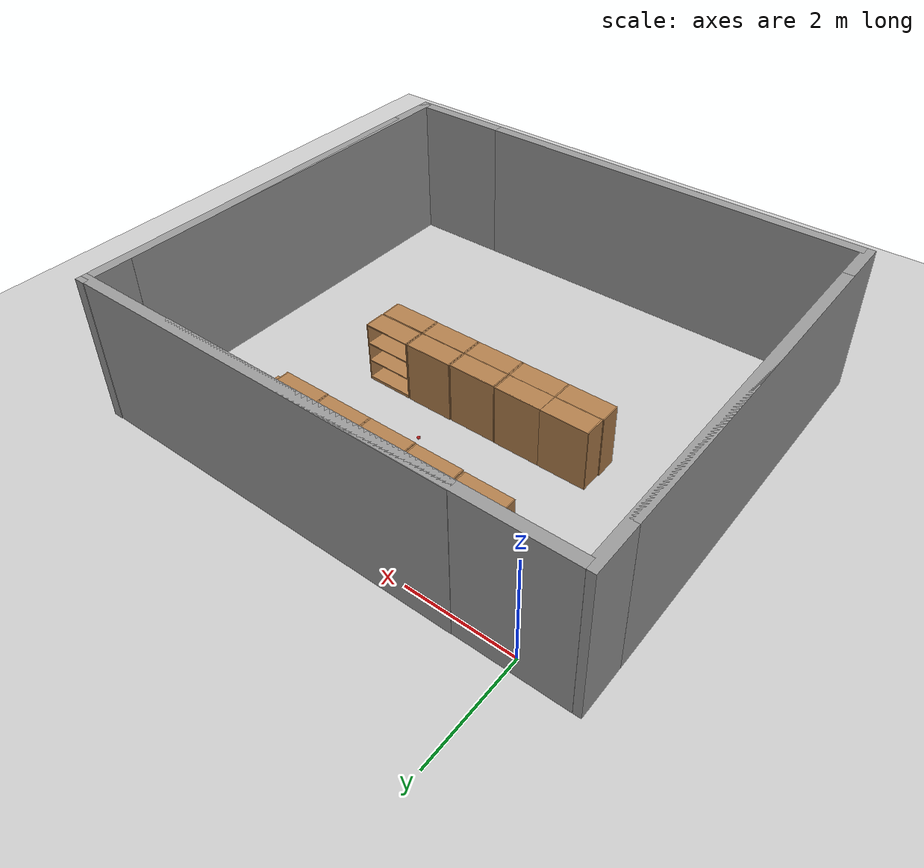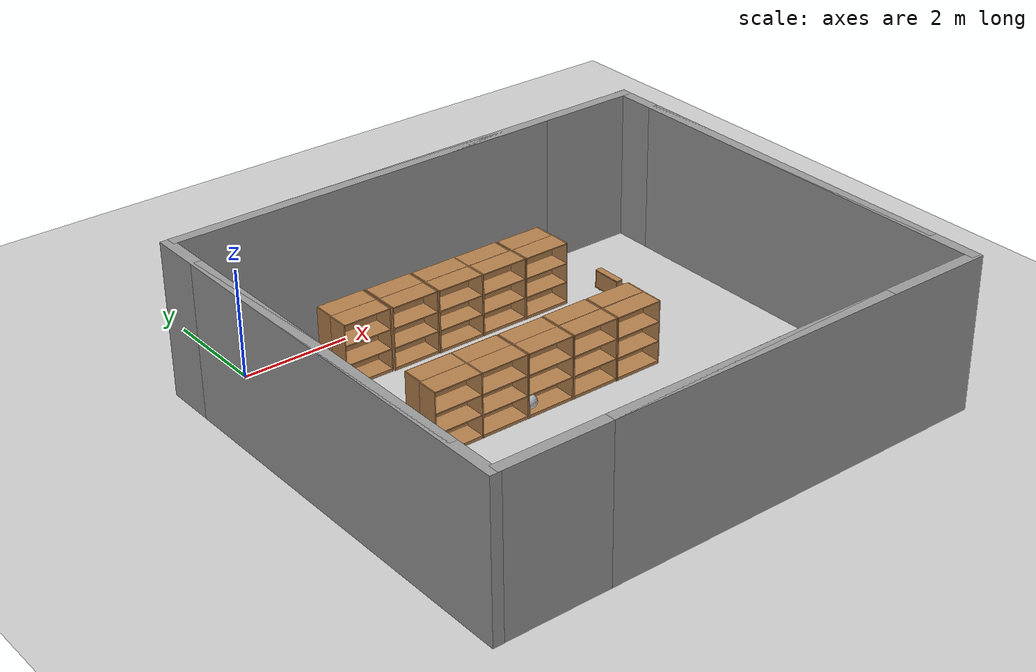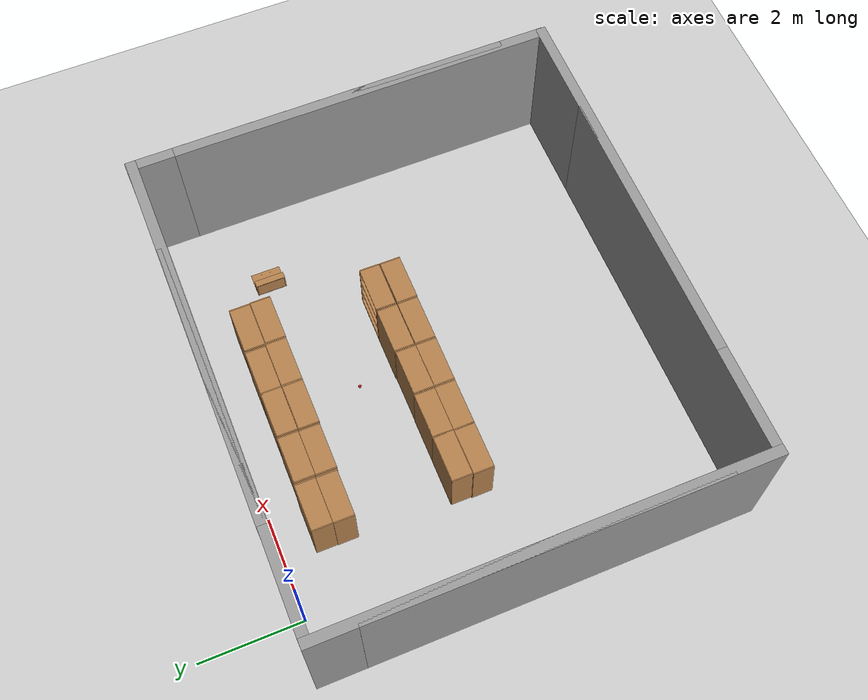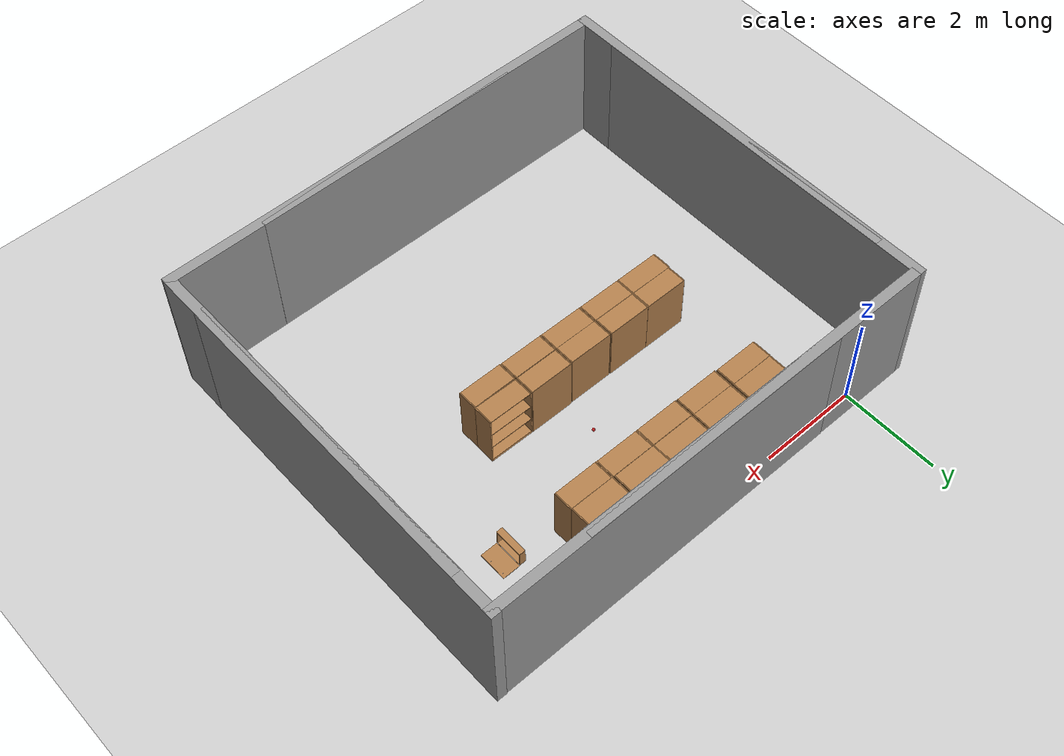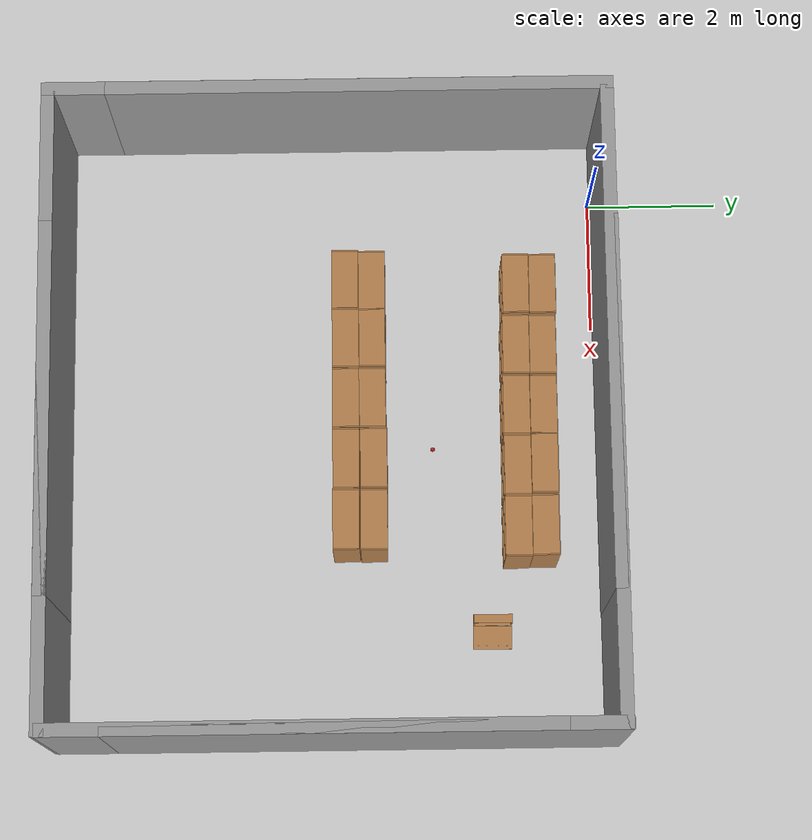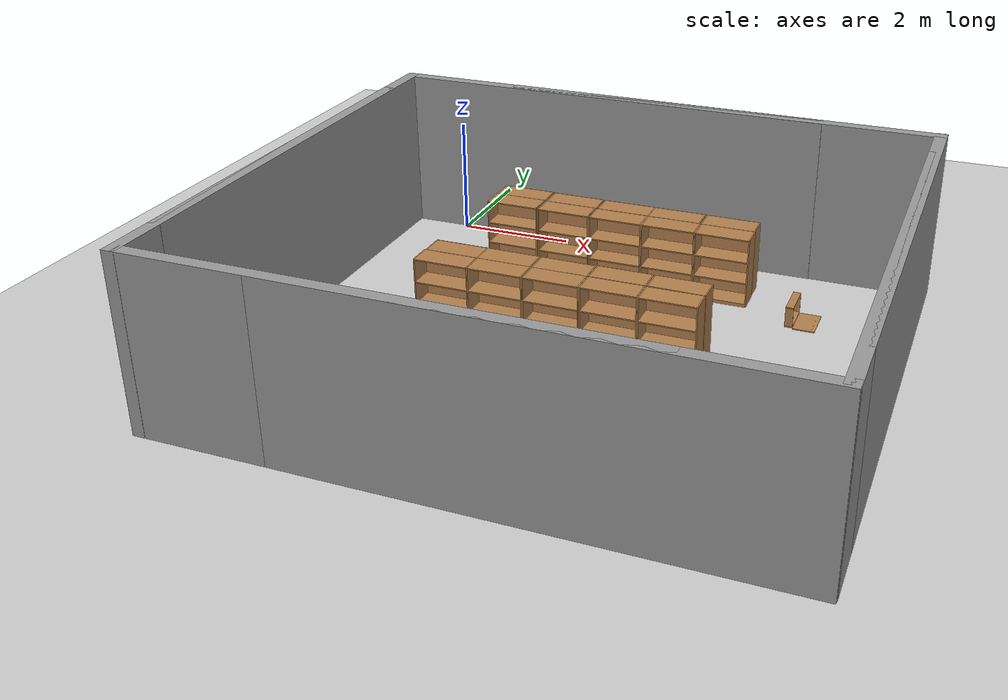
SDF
<sdf version="1.6">
 <world name="default">
  <light name="sun" type="directional">
   <pose>0 0 10 0 -0 0</pose>
   <diffuse>0.8 0.8 0.8 1</diffuse>
   <specular>0.2 0.2 0.2 1</specular>
   <attenuation>
    <range>1000</range>
    <constant>0.9</constant>
    <linear>0.01</linear>
    <quadratic>0.001</quadratic>
   </attenuation>
   <direction>-0.5 0.1 -0.9</direction>
  </light>
  <model name="ground_plane">
   <static>1</static>
   <link name="link">
    <collision name="collision">
     <geometry><plane><normal>0 0 1</normal><size>100 100</size></plane></geometry>
     <surface><friction><ode><mu>100</mu><mu2>50</mu2></ode></friction></surface>
    </collision>
    <visual name="visual">
     <cast_shadows>0</cast_shadows>
     <geometry><plane><normal>0 0 1</normal><size>100 100</size></plane></geometry>
     <material>
      <script><uri>file://media/materials/scripts/gazebo.material</uri><name>Gazebo/Grey</name></script>
     </material>
    </visual>
   </link>
  </model>
  <gravity>0 0 -9.8</gravity>
  <magnetic_field>6e-06 2.3e-05 -4.2e-05</magnetic_field>
  <atmosphere type="adiabatic"/>
  <physics name="default_physics" default="0" type="ode">
   <max_step_size>0.001</max_step_size>
   <real_time_factor>1</real_time_factor>
   <real_time_update_rate>1000</real_time_update_rate>
  </physics>
  <scene><ambient>0.4 0.4 0.4 1</ambient><background>0.7 0.7 0.7 1</background><shadows>1</shadows></scene>
  <spherical_coordinates>
   <surface_model>EARTH_WGS84</surface_model>
   <latitude_deg>0</latitude_deg>
   <longitude_deg>0</longitude_deg>
   <elevation>0</elevation>
   <heading_deg>0</heading_deg>
  </spherical_coordinates>
  <model name="bookshelf">
   <static>1</static>
   <link name="link">
    <inertial><mass>1</mass></inertial>
    <collision name="back">
     <pose>0 0.005 0.6 0 -0 0</pose>
     <geometry><box><size>0.9 0.01 1.2</size></box></geometry>
    </collision>
    <visual name="visual1">
     <pose>0 0.005 0.6 0 -0 0</pose>
     <geometry><box><size>0.9 0.01 1.2</size></box></geometry>
     <material>
      <script><uri>file://media/materials/scripts/gazebo.material</uri><name>Gazebo/Wood</name></script>
     </material>
    </visual>
    <collision name="left_side">
     <pose>0.45 -0.195 0.6 0 -0 0</pose>
     <geometry><box><size>0.02 0.4 1.2</size></box></geometry>
    </collision>
    <visual name="visual2">
     <pose>0.45 -0.195 0.6 0 -0 0</pose>
     <geometry><box><size>0.02 0.4 1.2</size></box></geometry>
     <material>
      <script><uri>file://media/materials/scripts/gazebo.material</uri><name>Gazebo/Wood</name></script>
     </material>
    </visual>
    <collision name="right_side">
     <pose>-0.45 -0.195 0.6 0 -0 0</pose>
     <geometry><box><size>0.02 0.4 1.2</size></box></geometry>
    </collision>
    <visual name="visual3">
     <pose>-0.45 -0.195 0.6 0 -0 0</pose>
     <geometry><box><size>0.02 0.4 1.2</size></box></geometry>
     <material>
      <script><uri>file://media/materials/scripts/gazebo.material</uri><name>Gazebo/Wood</name></script>
     </material>
    </visual>
    <collision name="bottom">
     <pose>0 -0.195 0.03 0 -0 0</pose>
     <geometry><box><size>0.88 0.4 0.06</size></box></geometry>
    </collision>
    <visual name="visual4">
     <pose>0 -0.195 0.03 0 -0 0</pose>
     <geometry><box><size>0.88 0.4 0.06</size></box></geometry>
     <material>
      <script><uri>file://media/materials/scripts/gazebo.material</uri><name>Gazebo/Wood</name></script>
     </material>
    </visual>
    <collision name="top">
     <pose>0 -0.195 1.19 0 -0 0</pose>
     <geometry><box><size>0.88 0.4 0.02</size></box></geometry>
    </collision>
    <visual name="visual5">
     <pose>0 -0.195 1.19 0 -0 0</pose>
     <geometry><box><size>0.88 0.4 0.02</size></box></geometry>
     <material>
      <script><uri>file://media/materials/scripts/gazebo.material</uri><name>Gazebo/Wood</name></script>
     </material>
    </visual>
    <collision name="low_shelf">
     <pose>0 -0.195 0.43 0 -0 0</pose>
     <geometry><box><size>0.88 0.4 0.02</size></box></geometry>
    </collision>
    <visual name="visual6">
     <pose>0 -0.195 0.43 0 -0 0</pose>
     <geometry><box><size>0.88 0.4 0.02</size></box></geometry>
     <material>
      <script><uri>file://media/materials/scripts/gazebo.material</uri><name>Gazebo/Wood</name></script>
     </material>
    </visual>
    <collision name="high_shelf">
     <pose>0 -0.195 0.8 0 -0 0</pose>
     <geometry><box><size>0.88 0.4 0.02</size></box></geometry>
    </collision>
    <visual name="visual7">
     <pose>0 -0.195 0.8 0 -0 0</pose>
     <geometry><box><size>0.88 0.4 0.02</size></box></geometry>
     <material>
      <script><uri>file://media/materials/scripts/gazebo.material</uri><name>Gazebo/Wood</name></script>
     </material>
    </visual>
   </link>
   <pose>1.54815 -1.01147 0 0 -0 0</pose>
  </model>
  <model name="bookshelf_clone">
   <static>1</static>
   <link name="link">
    <inertial><mass>1</mass></inertial>
    <collision name="back">
     <pose>0 0.005 0.6 0 -0 0</pose>
     <geometry><box><size>0.9 0.01 1.2</size></box></geometry>
    </collision>
    <visual name="visual1">
     <pose>0 0.005 0.6 0 -0 0</pose>
     <geometry><box><size>0.9 0.01 1.2</size></box></geometry>
     <material>
      <script><uri>file://media/materials/scripts/gazebo.material</uri><name>Gazebo/Wood</name></script>
     </material>
    </visual>
    <collision name="left_side">
     <pose>0.45 -0.195 0.6 0 -0 0</pose>
     <geometry><box><size>0.02 0.4 1.2</size></box></geometry>
    </collision>
    <visual name="visual2">
     <pose>0.45 -0.195 0.6 0 -0 0</pose>
     <geometry><box><size>0.02 0.4 1.2</size></box></geometry>
     <material>
      <script><uri>file://media/materials/scripts/gazebo.material</uri><name>Gazebo/Wood</name></script>
     </material>
    </visual>
    <collision name="right_side">
     <pose>-0.45 -0.195 0.6 0 -0 0</pose>
     <geometry><box><size>0.02 0.4 1.2</size></box></geometry>
    </collision>
    <visual name="visual3">
     <pose>-0.45 -0.195 0.6 0 -0 0</pose>
     <geometry><box><size>0.02 0.4 1.2</size></box></geometry>
     <material>
      <script><uri>file://media/materials/scripts/gazebo.material</uri><name>Gazebo/Wood</name></script>
     </material>
    </visual>
    <collision name="bottom">
     <pose>0 -0.195 0.03 0 -0 0</pose>
     <geometry><box><size>0.88 0.4 0.06</size></box></geometry>
    </collision>
    <visual name="visual4">
     <pose>0 -0.195 0.03 0 -0 0</pose>
     <geometry><box><size>0.88 0.4 0.06</size></box></geometry>
     <material>
      <script><uri>file://media/materials/scripts/gazebo.material</uri><name>Gazebo/Wood</name></script>
     </material>
    </visual>
    <collision name="top">
     <pose>0 -0.195 1.19 0 -0 0</pose>
     <geometry><box><size>0.88 0.4 0.02</size></box></geometry>
    </collision>
    <visual name="visual5">
     <pose>0 -0.195 1.19 0 -0 0</pose>
     <geometry><box><size>0.88 0.4 0.02</size></box></geometry>
     <material>
      <script><uri>file://media/materials/scripts/gazebo.material</uri><name>Gazebo/Wood</name></script>
     </material>
    </visual>
    <collision name="low_shelf">
     <pose>0 -0.195 0.43 0 -0 0</pose>
     <geometry><box><size>0.88 0.4 0.02</size></box></geometry>
    </collision>
    <visual name="visual6">
     <pose>0 -0.195 0.43 0 -0 0</pose>
     <geometry><box><size>0.88 0.4 0.02</size></box></geometry>
     <material>
      <script><uri>file://media/materials/scripts/gazebo.material</uri><name>Gazebo/Wood</name></script>
     </material>
    </visual>
    <collision name="high_shelf">
     <pose>0 -0.195 0.8 0 -0 0</pose>
     <geometry><box><size>0.88 0.4 0.02</size></box></geometry>
    </collision>
    <visual name="visual7">
     <pose>0 -0.195 0.8 0 -0 0</pose>
     <geometry><box><size>0.88 0.4 0.02</size></box></geometry>
     <material>
      <script><uri>file://media/materials/scripts/gazebo.material</uri><name>Gazebo/Wood</name></script>
     </material>
    </visual>
   </link>
   <pose>2.49358 -1.02826 0 0 -0 0</pose>
  </model>
  <model name="bookshelf_clone_0">
   <static>1</static>
   <link name="link">
    <inertial><mass>1</mass></inertial>
    <collision name="back">
     <pose>0 0.005 0.6 0 -0 0</pose>
     <geometry><box><size>0.9 0.01 1.2</size></box></geometry>
    </collision>
    <visual name="visual1">
     <pose>0 0.005 0.6 0 -0 0</pose>
     <geometry><box><size>0.9 0.01 1.2</size></box></geometry>
     <material>
      <script><uri>file://media/materials/scripts/gazebo.material</uri><name>Gazebo/Wood</name></script>
     </material>
    </visual>
    <collision name="left_side">
     <pose>0.45 -0.195 0.6 0 -0 0</pose>
     <geometry><box><size>0.02 0.4 1.2</size></box></geometry>
    </collision>
    <visual name="visual2">
     <pose>0.45 -0.195 0.6 0 -0 0</pose>
     <geometry><box><size>0.02 0.4 1.2</size></box></geometry>
     <material>
      <script><uri>file://media/materials/scripts/gazebo.material</uri><name>Gazebo/Wood</name></script>
     </material>
    </visual>
    <collision name="right_side">
     <pose>-0.45 -0.195 0.6 0 -0 0</pose>
     <geometry><box><size>0.02 0.4 1.2</size></box></geometry>
    </collision>
    <visual name="visual3">
     <pose>-0.45 -0.195 0.6 0 -0 0</pose>
     <geometry><box><size>0.02 0.4 1.2</size></box></geometry>
     <material>
      <script><uri>file://media/materials/scripts/gazebo.material</uri><name>Gazebo/Wood</name></script>
     </material>
    </visual>
    <collision name="bottom">
     <pose>0 -0.195 0.03 0 -0 0</pose>
     <geometry><box><size>0.88 0.4 0.06</size></box></geometry>
    </collision>
    <visual name="visual4">
     <pose>0 -0.195 0.03 0 -0 0</pose>
     <geometry><box><size>0.88 0.4 0.06</size></box></geometry>
     <material>
      <script><uri>file://media/materials/scripts/gazebo.material</uri><name>Gazebo/Wood</name></script>
     </material>
    </visual>
    <collision name="top">
     <pose>0 -0.195 1.19 0 -0 0</pose>
     <geometry><box><size>0.88 0.4 0.02</size></box></geometry>
    </collision>
    <visual name="visual5">
     <pose>0 -0.195 1.19 0 -0 0</pose>
     <geometry><box><size>0.88 0.4 0.02</size></box></geometry>
     <material>
      <script><uri>file://media/materials/scripts/gazebo.material</uri><name>Gazebo/Wood</name></script>
     </material>
    </visual>
    <collision name="low_shelf">
     <pose>0 -0.195 0.43 0 -0 0</pose>
     <geometry><box><size>0.88 0.4 0.02</size></box></geometry>
    </collision>
    <visual name="visual6">
     <pose>0 -0.195 0.43 0 -0 0</pose>
     <geometry><box><size>0.88 0.4 0.02</size></box></geometry>
     <material>
      <script><uri>file://media/materials/scripts/gazebo.material</uri><name>Gazebo/Wood</name></script>
     </material>
    </visual>
    <collision name="high_shelf">
     <pose>0 -0.195 0.8 0 -0 0</pose>
     <geometry><box><size>0.88 0.4 0.02</size></box></geometry>
    </collision>
    <visual name="visual7">
     <pose>0 -0.195 0.8 0 -0 0</pose>
     <geometry><box><size>0.88 0.4 0.02</size></box></geometry>
     <material>
      <script><uri>file://media/materials/scripts/gazebo.material</uri><name>Gazebo/Wood</name></script>
     </material>
    </visual>
   </link>
   <pose>3.42671 -1.03872 0 0 -0 0</pose>
  </model>
  <model name="bookshelf_clone_1">
   <static>1</static>
   <link name="link">
    <inertial><mass>1</mass></inertial>
    <collision name="back">
     <pose>0 0.005 0.6 0 -0 0</pose>
     <geometry><box><size>0.9 0.01 1.2</size></box></geometry>
    </collision>
    <visual name="visual1">
     <pose>0 0.005 0.6 0 -0 0</pose>
     <geometry><box><size>0.9 0.01 1.2</size></box></geometry>
     <material>
      <script><uri>file://media/materials/scripts/gazebo.material</uri><name>Gazebo/Wood</name></script>
     </material>
    </visual>
    <collision name="left_side">
     <pose>0.45 -0.195 0.6 0 -0 0</pose>
     <geometry><box><size>0.02 0.4 1.2</size></box></geometry>
    </collision>
    <visual name="visual2">
     <pose>0.45 -0.195 0.6 0 -0 0</pose>
     <geometry><box><size>0.02 0.4 1.2</size></box></geometry>
     <material>
      <script><uri>file://media/materials/scripts/gazebo.material</uri><name>Gazebo/Wood</name></script>
     </material>
    </visual>
    <collision name="right_side">
     <pose>-0.45 -0.195 0.6 0 -0 0</pose>
     <geometry><box><size>0.02 0.4 1.2</size></box></geometry>
    </collision>
    <visual name="visual3">
     <pose>-0.45 -0.195 0.6 0 -0 0</pose>
     <geometry><box><size>0.02 0.4 1.2</size></box></geometry>
     <material>
      <script><uri>file://media/materials/scripts/gazebo.material</uri><name>Gazebo/Wood</name></script>
     </material>
    </visual>
    <collision name="bottom">
     <pose>0 -0.195 0.03 0 -0 0</pose>
     <geometry><box><size>0.88 0.4 0.06</size></box></geometry>
    </collision>
    <visual name="visual4">
     <pose>0 -0.195 0.03 0 -0 0</pose>
     <geometry><box><size>0.88 0.4 0.06</size></box></geometry>
     <material>
      <script><uri>file://media/materials/scripts/gazebo.material</uri><name>Gazebo/Wood</name></script>
     </material>
    </visual>
    <collision name="top">
     <pose>0 -0.195 1.19 0 -0 0</pose>
     <geometry><box><size>0.88 0.4 0.02</size></box></geometry>
    </collision>
    <visual name="visual5">
     <pose>0 -0.195 1.19 0 -0 0</pose>
     <geometry><box><size>0.88 0.4 0.02</size></box></geometry>
     <material>
      <script><uri>file://media/materials/scripts/gazebo.material</uri><name>Gazebo/Wood</name></script>
     </material>
    </visual>
    <collision name="low_shelf">
     <pose>0 -0.195 0.43 0 -0 0</pose>
     <geometry><box><size>0.88 0.4 0.02</size></box></geometry>
    </collision>
    <visual name="visual6">
     <pose>0 -0.195 0.43 0 -0 0</pose>
     <geometry><box><size>0.88 0.4 0.02</size></box></geometry>
     <material>
      <script><uri>file://media/materials/scripts/gazebo.material</uri><name>Gazebo/Wood</name></script>
     </material>
    </visual>
    <collision name="high_shelf">
     <pose>0 -0.195 0.8 0 -0 0</pose>
     <geometry><box><size>0.88 0.4 0.02</size></box></geometry>
    </collision>
    <visual name="visual7">
     <pose>0 -0.195 0.8 0 -0 0</pose>
     <geometry><box><size>0.88 0.4 0.02</size></box></geometry>
     <material>
      <script><uri>file://media/materials/scripts/gazebo.material</uri><name>Gazebo/Wood</name></script>
     </material>
    </visual>
   </link>
   <pose>4.34765 -1.03859 0 0 -0 0</pose>
  </model>
  <model name="bookshelf_clone_2">
   <static>1</static>
   <link name="link">
    <inertial><mass>1</mass></inertial>
    <collision name="back">
     <pose>0 0.005 0.6 0 -0 0</pose>
     <geometry><box><size>0.9 0.01 1.2</size></box></geometry>
    </collision>
    <visual name="visual1">
     <pose>0 0.005 0.6 0 -0 0</pose>
     <geometry><box><size>0.9 0.01 1.2</size></box></geometry>
     <material>
      <script><uri>file://media/materials/scripts/gazebo.material</uri><name>Gazebo/Wood</name></script>
     </material>
    </visual>
    <collision name="left_side">
     <pose>0.45 -0.195 0.6 0 -0 0</pose>
     <geometry><box><size>0.02 0.4 1.2</size></box></geometry>
    </collision>
    <visual name="visual2">
     <pose>0.45 -0.195 0.6 0 -0 0</pose>
     <geometry><box><size>0.02 0.4 1.2</size></box></geometry>
     <material>
      <script><uri>file://media/materials/scripts/gazebo.material</uri><name>Gazebo/Wood</name></script>
     </material>
    </visual>
    <collision name="right_side">
     <pose>-0.45 -0.195 0.6 0 -0 0</pose>
     <geometry><box><size>0.02 0.4 1.2</size></box></geometry>
    </collision>
    <visual name="visual3">
     <pose>-0.45 -0.195 0.6 0 -0 0</pose>
     <geometry><box><size>0.02 0.4 1.2</size></box></geometry>
     <material>
      <script><uri>file://media/materials/scripts/gazebo.material</uri><name>Gazebo/Wood</name></script>
     </material>
    </visual>
    <collision name="bottom">
     <pose>0 -0.195 0.03 0 -0 0</pose>
     <geometry><box><size>0.88 0.4 0.06</size></box></geometry>
    </collision>
    <visual name="visual4">
     <pose>0 -0.195 0.03 0 -0 0</pose>
     <geometry><box><size>0.88 0.4 0.06</size></box></geometry>
     <material>
      <script><uri>file://media/materials/scripts/gazebo.material</uri><name>Gazebo/Wood</name></script>
     </material>
    </visual>
    <collision name="top">
     <pose>0 -0.195 1.19 0 -0 0</pose>
     <geometry><box><size>0.88 0.4 0.02</size></box></geometry>
    </collision>
    <visual name="visual5">
     <pose>0 -0.195 1.19 0 -0 0</pose>
     <geometry><box><size>0.88 0.4 0.02</size></box></geometry>
     <material>
      <script><uri>file://media/materials/scripts/gazebo.material</uri><name>Gazebo/Wood</name></script>
     </material>
    </visual>
    <collision name="low_shelf">
     <pose>0 -0.195 0.43 0 -0 0</pose>
     <geometry><box><size>0.88 0.4 0.02</size></box></geometry>
    </collision>
    <visual name="visual6">
     <pose>0 -0.195 0.43 0 -0 0</pose>
     <geometry><box><size>0.88 0.4 0.02</size></box></geometry>
     <material>
      <script><uri>file://media/materials/scripts/gazebo.material</uri><name>Gazebo/Wood</name></script>
     </material>
    </visual>
    <collision name="high_shelf">
     <pose>0 -0.195 0.8 0 -0 0</pose>
     <geometry><box><size>0.88 0.4 0.02</size></box></geometry>
    </collision>
    <visual name="visual7">
     <pose>0 -0.195 0.8 0 -0 0</pose>
     <geometry><box><size>0.88 0.4 0.02</size></box></geometry>
     <material>
      <script><uri>file://media/materials/scripts/gazebo.material</uri><name>Gazebo/Wood</name></script>
     </material>
    </visual>
   </link>
   <pose>5.27168 -1.04513 0 0 -0 0</pose>
  </model>
  <model name="bookshelf_clone_3">
   <static>1</static>
   <link name="link">
    <inertial><mass>1</mass></inertial>
    <collision name="back">
     <pose>0 0.005 0.6 0 -0 0</pose>
     <geometry><box><size>0.9 0.01 1.2</size></box></geometry>
    </collision>
    <visual name="visual1">
     <pose>0 0.005 0.6 0 -0 0</pose>
     <geometry><box><size>0.9 0.01 1.2</size></box></geometry>
     <material>
      <script><uri>file://media/materials/scripts/gazebo.material</uri><name>Gazebo/Wood</name></script>
     </material>
    </visual>
    <collision name="left_side">
     <pose>0.45 -0.195 0.6 0 -0 0</pose>
     <geometry><box><size>0.02 0.4 1.2</size></box></geometry>
    </collision>
    <visual name="visual2">
     <pose>0.45 -0.195 0.6 0 -0 0</pose>
     <geometry><box><size>0.02 0.4 1.2</size></box></geometry>
     <material>
      <script><uri>file://media/materials/scripts/gazebo.material</uri><name>Gazebo/Wood</name></script>
     </material>
    </visual>
    <collision name="right_side">
     <pose>-0.45 -0.195 0.6 0 -0 0</pose>
     <geometry><box><size>0.02 0.4 1.2</size></box></geometry>
    </collision>
    <visual name="visual3">
     <pose>-0.45 -0.195 0.6 0 -0 0</pose>
     <geometry><box><size>0.02 0.4 1.2</size></box></geometry>
     <material>
      <script><uri>file://media/materials/scripts/gazebo.material</uri><name>Gazebo/Wood</name></script>
     </material>
    </visual>
    <collision name="bottom">
     <pose>0 -0.195 0.03 0 -0 0</pose>
     <geometry><box><size>0.88 0.4 0.06</size></box></geometry>
    </collision>
    <visual name="visual4">
     <pose>0 -0.195 0.03 0 -0 0</pose>
     <geometry><box><size>0.88 0.4 0.06</size></box></geometry>
     <material>
      <script><uri>file://media/materials/scripts/gazebo.material</uri><name>Gazebo/Wood</name></script>
     </material>
    </visual>
    <collision name="top">
     <pose>0 -0.195 1.19 0 -0 0</pose>
     <geometry><box><size>0.88 0.4 0.02</size></box></geometry>
    </collision>
    <visual name="visual5">
     <pose>0 -0.195 1.19 0 -0 0</pose>
     <geometry><box><size>0.88 0.4 0.02</size></box></geometry>
     <material>
      <script><uri>file://media/materials/scripts/gazebo.material</uri><name>Gazebo/Wood</name></script>
     </material>
    </visual>
    <collision name="low_shelf">
     <pose>0 -0.195 0.43 0 -0 0</pose>
     <geometry><box><size>0.88 0.4 0.02</size></box></geometry>
    </collision>
    <visual name="visual6">
     <pose>0 -0.195 0.43 0 -0 0</pose>
     <geometry><box><size>0.88 0.4 0.02</size></box></geometry>
     <material>
      <script><uri>file://media/materials/scripts/gazebo.material</uri><name>Gazebo/Wood</name></script>
     </material>
    </visual>
    <collision name="high_shelf">
     <pose>0 -0.195 0.8 0 -0 0</pose>
     <geometry><box><size>0.88 0.4 0.02</size></box></geometry>
    </collision>
    <visual name="visual7">
     <pose>0 -0.195 0.8 0 -0 0</pose>
     <geometry><box><size>0.88 0.4 0.02</size></box></geometry>
     <material>
      <script><uri>file://media/materials/scripts/gazebo.material</uri><name>Gazebo/Wood</name></script>
     </material>
    </visual>
   </link>
   <pose>1.45828 -3.59625 0 0 -0 0</pose>
  </model>
  <model name="bookshelf_clone_4">
   <static>1</static>
   <link name="link">
    <inertial><mass>1</mass></inertial>
    <collision name="back">
     <pose>0 0.005 0.6 0 -0 0</pose>
     <geometry><box><size>0.9 0.01 1.2</size></box></geometry>
    </collision>
    <visual name="visual1">
     <pose>0 0.005 0.6 0 -0 0</pose>
     <geometry><box><size>0.9 0.01 1.2</size></box></geometry>
     <material>
      <script><uri>file://media/materials/scripts/gazebo.material</uri><name>Gazebo/Wood</name></script>
     </material>
    </visual>
    <collision name="left_side">
     <pose>0.45 -0.195 0.6 0 -0 0</pose>
     <geometry><box><size>0.02 0.4 1.2</size></box></geometry>
    </collision>
    <visual name="visual2">
     <pose>0.45 -0.195 0.6 0 -0 0</pose>
     <geometry><box><size>0.02 0.4 1.2</size></box></geometry>
     <material>
      <script><uri>file://media/materials/scripts/gazebo.material</uri><name>Gazebo/Wood</name></script>
     </material>
    </visual>
    <collision name="right_side">
     <pose>-0.45 -0.195 0.6 0 -0 0</pose>
     <geometry><box><size>0.02 0.4 1.2</size></box></geometry>
    </collision>
    <visual name="visual3">
     <pose>-0.45 -0.195 0.6 0 -0 0</pose>
     <geometry><box><size>0.02 0.4 1.2</size></box></geometry>
     <material>
      <script><uri>file://media/materials/scripts/gazebo.material</uri><name>Gazebo/Wood</name></script>
     </material>
    </visual>
    <collision name="bottom">
     <pose>0 -0.195 0.03 0 -0 0</pose>
     <geometry><box><size>0.88 0.4 0.06</size></box></geometry>
    </collision>
    <visual name="visual4">
     <pose>0 -0.195 0.03 0 -0 0</pose>
     <geometry><box><size>0.88 0.4 0.06</size></box></geometry>
     <material>
      <script><uri>file://media/materials/scripts/gazebo.material</uri><name>Gazebo/Wood</name></script>
     </material>
    </visual>
    <collision name="top">
     <pose>0 -0.195 1.19 0 -0 0</pose>
     <geometry><box><size>0.88 0.4 0.02</size></box></geometry>
    </collision>
    <visual name="visual5">
     <pose>0 -0.195 1.19 0 -0 0</pose>
     <geometry><box><size>0.88 0.4 0.02</size></box></geometry>
     <material>
      <script><uri>file://media/materials/scripts/gazebo.material</uri><name>Gazebo/Wood</name></script>
     </material>
    </visual>
    <collision name="low_shelf">
     <pose>0 -0.195 0.43 0 -0 0</pose>
     <geometry><box><size>0.88 0.4 0.02</size></box></geometry>
    </collision>
    <visual name="visual6">
     <pose>0 -0.195 0.43 0 -0 0</pose>
     <geometry><box><size>0.88 0.4 0.02</size></box></geometry>
     <material>
      <script><uri>file://media/materials/scripts/gazebo.material</uri><name>Gazebo/Wood</name></script>
     </material>
    </visual>
    <collision name="high_shelf">
     <pose>0 -0.195 0.8 0 -0 0</pose>
     <geometry><box><size>0.88 0.4 0.02</size></box></geometry>
    </collision>
    <visual name="visual7">
     <pose>0 -0.195 0.8 0 -0 0</pose>
     <geometry><box><size>0.88 0.4 0.02</size></box></geometry>
     <material>
      <script><uri>file://media/materials/scripts/gazebo.material</uri><name>Gazebo/Wood</name></script>
     </material>
    </visual>
   </link>
   <pose>2.36721 -3.5964 0 0 -0 0</pose>
  </model>
  <model name="bookshelf_clone_5">
   <static>1</static>
   <link name="link">
    <inertial><mass>1</mass></inertial>
    <collision name="back">
     <pose>0 0.005 0.6 0 -0 0</pose>
     <geometry><box><size>0.9 0.01 1.2</size></box></geometry>
    </collision>
    <visual name="visual1">
     <pose>0 0.005 0.6 0 -0 0</pose>
     <geometry><box><size>0.9 0.01 1.2</size></box></geometry>
     <material>
      <script><uri>file://media/materials/scripts/gazebo.material</uri><name>Gazebo/Wood</name></script>
     </material>
    </visual>
    <collision name="left_side">
     <pose>0.45 -0.195 0.6 0 -0 0</pose>
     <geometry><box><size>0.02 0.4 1.2</size></box></geometry>
    </collision>
    <visual name="visual2">
     <pose>0.45 -0.195 0.6 0 -0 0</pose>
     <geometry><box><size>0.02 0.4 1.2</size></box></geometry>
     <material>
      <script><uri>file://media/materials/scripts/gazebo.material</uri><name>Gazebo/Wood</name></script>
     </material>
    </visual>
    <collision name="right_side">
     <pose>-0.45 -0.195 0.6 0 -0 0</pose>
     <geometry><box><size>0.02 0.4 1.2</size></box></geometry>
    </collision>
    <visual name="visual3">
     <pose>-0.45 -0.195 0.6 0 -0 0</pose>
     <geometry><box><size>0.02 0.4 1.2</size></box></geometry>
     <material>
      <script><uri>file://media/materials/scripts/gazebo.material</uri><name>Gazebo/Wood</name></script>
     </material>
    </visual>
    <collision name="bottom">
     <pose>0 -0.195 0.03 0 -0 0</pose>
     <geometry><box><size>0.88 0.4 0.06</size></box></geometry>
    </collision>
    <visual name="visual4">
     <pose>0 -0.195 0.03 0 -0 0</pose>
     <geometry><box><size>0.88 0.4 0.06</size></box></geometry>
     <material>
      <script><uri>file://media/materials/scripts/gazebo.material</uri><name>Gazebo/Wood</name></script>
     </material>
    </visual>
    <collision name="top">
     <pose>0 -0.195 1.19 0 -0 0</pose>
     <geometry><box><size>0.88 0.4 0.02</size></box></geometry>
    </collision>
    <visual name="visual5">
     <pose>0 -0.195 1.19 0 -0 0</pose>
     <geometry><box><size>0.88 0.4 0.02</size></box></geometry>
     <material>
      <script><uri>file://media/materials/scripts/gazebo.material</uri><name>Gazebo/Wood</name></script>
     </material>
    </visual>
    <collision name="low_shelf">
     <pose>0 -0.195 0.43 0 -0 0</pose>
     <geometry><box><size>0.88 0.4 0.02</size></box></geometry>
    </collision>
    <visual name="visual6">
     <pose>0 -0.195 0.43 0 -0 0</pose>
     <geometry><box><size>0.88 0.4 0.02</size></box></geometry>
     <material>
      <script><uri>file://media/materials/scripts/gazebo.material</uri><name>Gazebo/Wood</name></script>
     </material>
    </visual>
    <collision name="high_shelf">
     <pose>0 -0.195 0.8 0 -0 0</pose>
     <geometry><box><size>0.88 0.4 0.02</size></box></geometry>
    </collision>
    <visual name="visual7">
     <pose>0 -0.195 0.8 0 -0 0</pose>
     <geometry><box><size>0.88 0.4 0.02</size></box></geometry>
     <material>
      <script><uri>file://media/materials/scripts/gazebo.material</uri><name>Gazebo/Wood</name></script>
     </material>
    </visual>
   </link>
   <pose>3.29215 -3.59972 0 0 -0 0</pose>
  </model>
  <model name="bookshelf_clone_6">
   <static>1</static>
   <link name="link">
    <inertial><mass>1</mass></inertial>
    <collision name="back">
     <pose>0 0.005 0.6 0 -0 0</pose>
     <geometry><box><size>0.9 0.01 1.2</size></box></geometry>
    </collision>
    <visual name="visual1">
     <pose>0 0.005 0.6 0 -0 0</pose>
     <geometry><box><size>0.9 0.01 1.2</size></box></geometry>
     <material>
      <script><uri>file://media/materials/scripts/gazebo.material</uri><name>Gazebo/Wood</name></script>
     </material>
    </visual>
    <collision name="left_side">
     <pose>0.45 -0.195 0.6 0 -0 0</pose>
     <geometry><box><size>0.02 0.4 1.2</size></box></geometry>
    </collision>
    <visual name="visual2">
     <pose>0.45 -0.195 0.6 0 -0 0</pose>
     <geometry><box><size>0.02 0.4 1.2</size></box></geometry>
     <material>
      <script><uri>file://media/materials/scripts/gazebo.material</uri><name>Gazebo/Wood</name></script>
     </material>
    </visual>
    <collision name="right_side">
     <pose>-0.45 -0.195 0.6 0 -0 0</pose>
     <geometry><box><size>0.02 0.4 1.2</size></box></geometry>
    </collision>
    <visual name="visual3">
     <pose>-0.45 -0.195 0.6 0 -0 0</pose>
     <geometry><box><size>0.02 0.4 1.2</size></box></geometry>
     <material>
      <script><uri>file://media/materials/scripts/gazebo.material</uri><name>Gazebo/Wood</name></script>
     </material>
    </visual>
    <collision name="bottom">
     <pose>0 -0.195 0.03 0 -0 0</pose>
     <geometry><box><size>0.88 0.4 0.06</size></box></geometry>
    </collision>
    <visual name="visual4">
     <pose>0 -0.195 0.03 0 -0 0</pose>
     <geometry><box><size>0.88 0.4 0.06</size></box></geometry>
     <material>
      <script><uri>file://media/materials/scripts/gazebo.material</uri><name>Gazebo/Wood</name></script>
     </material>
    </visual>
    <collision name="top">
     <pose>0 -0.195 1.19 0 -0 0</pose>
     <geometry><box><size>0.88 0.4 0.02</size></box></geometry>
    </collision>
    <visual name="visual5">
     <pose>0 -0.195 1.19 0 -0 0</pose>
     <geometry><box><size>0.88 0.4 0.02</size></box></geometry>
     <material>
      <script><uri>file://media/materials/scripts/gazebo.material</uri><name>Gazebo/Wood</name></script>
     </material>
    </visual>
    <collision name="low_shelf">
     <pose>0 -0.195 0.43 0 -0 0</pose>
     <geometry><box><size>0.88 0.4 0.02</size></box></geometry>
    </collision>
    <visual name="visual6">
     <pose>0 -0.195 0.43 0 -0 0</pose>
     <geometry><box><size>0.88 0.4 0.02</size></box></geometry>
     <material>
      <script><uri>file://media/materials/scripts/gazebo.material</uri><name>Gazebo/Wood</name></script>
     </material>
    </visual>
    <collision name="high_shelf">
     <pose>0 -0.195 0.8 0 -0 0</pose>
     <geometry><box><size>0.88 0.4 0.02</size></box></geometry>
    </collision>
    <visual name="visual7">
     <pose>0 -0.195 0.8 0 -0 0</pose>
     <geometry><box><size>0.88 0.4 0.02</size></box></geometry>
     <material>
      <script><uri>file://media/materials/scripts/gazebo.material</uri><name>Gazebo/Wood</name></script>
     </material>
    </visual>
   </link>
   <pose>4.21731 -3.60193 0 0 -0 0</pose>
  </model>
  <model name="bookshelf_clone_7">
   <static>1</static>
   <link name="link">
    <inertial><mass>1</mass></inertial>
    <collision name="back">
     <pose>0 0.005 0.6 0 -0 0</pose>
     <geometry><box><size>0.9 0.01 1.2</size></box></geometry>
    </collision>
    <visual name="visual1">
     <pose>0 0.005 0.6 0 -0 0</pose>
     <geometry><box><size>0.9 0.01 1.2</size></box></geometry>
     <material>
      <script><uri>file://media/materials/scripts/gazebo.material</uri><name>Gazebo/Wood</name></script>
     </material>
    </visual>
    <collision name="left_side">
     <pose>0.45 -0.195 0.6 0 -0 0</pose>
     <geometry><box><size>0.02 0.4 1.2</size></box></geometry>
    </collision>
    <visual name="visual2">
     <pose>0.45 -0.195 0.6 0 -0 0</pose>
     <geometry><box><size>0.02 0.4 1.2</size></box></geometry>
     <material>
      <script><uri>file://media/materials/scripts/gazebo.material</uri><name>Gazebo/Wood</name></script>
     </material>
    </visual>
    <collision name="right_side">
     <pose>-0.45 -0.195 0.6 0 -0 0</pose>
     <geometry><box><size>0.02 0.4 1.2</size></box></geometry>
    </collision>
    <visual name="visual3">
     <pose>-0.45 -0.195 0.6 0 -0 0</pose>
     <geometry><box><size>0.02 0.4 1.2</size></box></geometry>
     <material>
      <script><uri>file://media/materials/scripts/gazebo.material</uri><name>Gazebo/Wood</name></script>
     </material>
    </visual>
    <collision name="bottom">
     <pose>0 -0.195 0.03 0 -0 0</pose>
     <geometry><box><size>0.88 0.4 0.06</size></box></geometry>
    </collision>
    <visual name="visual4">
     <pose>0 -0.195 0.03 0 -0 0</pose>
     <geometry><box><size>0.88 0.4 0.06</size></box></geometry>
     <material>
      <script><uri>file://media/materials/scripts/gazebo.material</uri><name>Gazebo/Wood</name></script>
     </material>
    </visual>
    <collision name="top">
     <pose>0 -0.195 1.19 0 -0 0</pose>
     <geometry><box><size>0.88 0.4 0.02</size></box></geometry>
    </collision>
    <visual name="visual5">
     <pose>0 -0.195 1.19 0 -0 0</pose>
     <geometry><box><size>0.88 0.4 0.02</size></box></geometry>
     <material>
      <script><uri>file://media/materials/scripts/gazebo.material</uri><name>Gazebo/Wood</name></script>
     </material>
    </visual>
    <collision name="low_shelf">
     <pose>0 -0.195 0.43 0 -0 0</pose>
     <geometry><box><size>0.88 0.4 0.02</size></box></geometry>
    </collision>
    <visual name="visual6">
     <pose>0 -0.195 0.43 0 -0 0</pose>
     <geometry><box><size>0.88 0.4 0.02</size></box></geometry>
     <material>
      <script><uri>file://media/materials/scripts/gazebo.material</uri><name>Gazebo/Wood</name></script>
     </material>
    </visual>
    <collision name="high_shelf">
     <pose>0 -0.195 0.8 0 -0 0</pose>
     <geometry><box><size>0.88 0.4 0.02</size></box></geometry>
    </collision>
    <visual name="visual7">
     <pose>0 -0.195 0.8 0 -0 0</pose>
     <geometry><box><size>0.88 0.4 0.02</size></box></geometry>
     <material>
      <script><uri>file://media/materials/scripts/gazebo.material</uri><name>Gazebo/Wood</name></script>
     </material>
    </visual>
   </link>
   <pose>5.14115 -3.60977 0 0 -0 0</pose>
  </model>
  <model name="bookshelf_clone_8">
   <static>1</static>
   <link name="link">
    <inertial><mass>1</mass></inertial>
    <collision name="back">
     <pose>0 0.005 0.6 0 -0 0</pose>
     <geometry><box><size>0.9 0.01 1.2</size></box></geometry>
    </collision>
    <visual name="visual1">
     <pose>0 0.005 0.6 0 -0 0</pose>
     <geometry><box><size>0.9 0.01 1.2</size></box></geometry>
     <material>
      <script><uri>file://media/materials/scripts/gazebo.material</uri><name>Gazebo/Wood</name></script>
     </material>
    </visual>
    <collision name="left_side">
     <pose>0.45 -0.195 0.6 0 -0 0</pose>
     <geometry><box><size>0.02 0.4 1.2</size></box></geometry>
    </collision>
    <visual name="visual2">
     <pose>0.45 -0.195 0.6 0 -0 0</pose>
     <geometry><box><size>0.02 0.4 1.2</size></box></geometry>
     <material>
      <script><uri>file://media/materials/scripts/gazebo.material</uri><name>Gazebo/Wood</name></script>
     </material>
    </visual>
    <collision name="right_side">
     <pose>-0.45 -0.195 0.6 0 -0 0</pose>
     <geometry><box><size>0.02 0.4 1.2</size></box></geometry>
    </collision>
    <visual name="visual3">
     <pose>-0.45 -0.195 0.6 0 -0 0</pose>
     <geometry><box><size>0.02 0.4 1.2</size></box></geometry>
     <material>
      <script><uri>file://media/materials/scripts/gazebo.material</uri><name>Gazebo/Wood</name></script>
     </material>
    </visual>
    <collision name="bottom">
     <pose>0 -0.195 0.03 0 -0 0</pose>
     <geometry><box><size>0.88 0.4 0.06</size></box></geometry>
    </collision>
    <visual name="visual4">
     <pose>0 -0.195 0.03 0 -0 0</pose>
     <geometry><box><size>0.88 0.4 0.06</size></box></geometry>
     <material>
      <script><uri>file://media/materials/scripts/gazebo.material</uri><name>Gazebo/Wood</name></script>
     </material>
    </visual>
    <collision name="top">
     <pose>0 -0.195 1.19 0 -0 0</pose>
     <geometry><box><size>0.88 0.4 0.02</size></box></geometry>
    </collision>
    <visual name="visual5">
     <pose>0 -0.195 1.19 0 -0 0</pose>
     <geometry><box><size>0.88 0.4 0.02</size></box></geometry>
     <material>
      <script><uri>file://media/materials/scripts/gazebo.material</uri><name>Gazebo/Wood</name></script>
     </material>
    </visual>
    <collision name="low_shelf">
     <pose>0 -0.195 0.43 0 -0 0</pose>
     <geometry><box><size>0.88 0.4 0.02</size></box></geometry>
    </collision>
    <visual name="visual6">
     <pose>0 -0.195 0.43 0 -0 0</pose>
     <geometry><box><size>0.88 0.4 0.02</size></box></geometry>
     <material>
      <script><uri>file://media/materials/scripts/gazebo.material</uri><name>Gazebo/Wood</name></script>
     </material>
    </visual>
    <collision name="high_shelf">
     <pose>0 -0.195 0.8 0 -0 0</pose>
     <geometry><box><size>0.88 0.4 0.02</size></box></geometry>
    </collision>
    <visual name="visual7">
     <pose>0 -0.195 0.8 0 -0 0</pose>
     <geometry><box><size>0.88 0.4 0.02</size></box></geometry>
     <material>
      <script><uri>file://media/materials/scripts/gazebo.material</uri><name>Gazebo/Wood</name></script>
     </material>
    </visual>
   </link>
   <pose>5.14519 -3.58129 0 0 -0 3.13199</pose>
  </model>
  <model name="bookshelf_clone_9">
   <static>1</static>
   <link name="link">
    <inertial><mass>1</mass></inertial>
    <collision name="back">
     <pose>0 0.005 0.6 0 -0 0</pose>
     <geometry><box><size>0.9 0.01 1.2</size></box></geometry>
    </collision>
    <visual name="visual1">
     <pose>0 0.005 0.6 0 -0 0</pose>
     <geometry><box><size>0.9 0.01 1.2</size></box></geometry>
     <material>
      <script><uri>file://media/materials/scripts/gazebo.material</uri><name>Gazebo/Wood</name></script>
     </material>
    </visual>
    <collision name="left_side">
     <pose>0.45 -0.195 0.6 0 -0 0</pose>
     <geometry><box><size>0.02 0.4 1.2</size></box></geometry>
    </collision>
    <visual name="visual2">
     <pose>0.45 -0.195 0.6 0 -0 0</pose>
     <geometry><box><size>0.02 0.4 1.2</size></box></geometry>
     <material>
      <script><uri>file://media/materials/scripts/gazebo.material</uri><name>Gazebo/Wood</name></script>
     </material>
    </visual>
    <collision name="right_side">
     <pose>-0.45 -0.195 0.6 0 -0 0</pose>
     <geometry><box><size>0.02 0.4 1.2</size></box></geometry>
    </collision>
    <visual name="visual3">
     <pose>-0.45 -0.195 0.6 0 -0 0</pose>
     <geometry><box><size>0.02 0.4 1.2</size></box></geometry>
     <material>
      <script><uri>file://media/materials/scripts/gazebo.material</uri><name>Gazebo/Wood</name></script>
     </material>
    </visual>
    <collision name="bottom">
     <pose>0 -0.195 0.03 0 -0 0</pose>
     <geometry><box><size>0.88 0.4 0.06</size></box></geometry>
    </collision>
    <visual name="visual4">
     <pose>0 -0.195 0.03 0 -0 0</pose>
     <geometry><box><size>0.88 0.4 0.06</size></box></geometry>
     <material>
      <script><uri>file://media/materials/scripts/gazebo.material</uri><name>Gazebo/Wood</name></script>
     </material>
    </visual>
    <collision name="top">
     <pose>0 -0.195 1.19 0 -0 0</pose>
     <geometry><box><size>0.88 0.4 0.02</size></box></geometry>
    </collision>
    <visual name="visual5">
     <pose>0 -0.195 1.19 0 -0 0</pose>
     <geometry><box><size>0.88 0.4 0.02</size></box></geometry>
     <material>
      <script><uri>file://media/materials/scripts/gazebo.material</uri><name>Gazebo/Wood</name></script>
     </material>
    </visual>
    <collision name="low_shelf">
     <pose>0 -0.195 0.43 0 -0 0</pose>
     <geometry><box><size>0.88 0.4 0.02</size></box></geometry>
    </collision>
    <visual name="visual6">
     <pose>0 -0.195 0.43 0 -0 0</pose>
     <geometry><box><size>0.88 0.4 0.02</size></box></geometry>
     <material>
      <script><uri>file://media/materials/scripts/gazebo.material</uri><name>Gazebo/Wood</name></script>
     </material>
    </visual>
    <collision name="high_shelf">
     <pose>0 -0.195 0.8 0 -0 0</pose>
     <geometry><box><size>0.88 0.4 0.02</size></box></geometry>
    </collision>
    <visual name="visual7">
     <pose>0 -0.195 0.8 0 -0 0</pose>
     <geometry><box><size>0.88 0.4 0.02</size></box></geometry>
     <material>
      <script><uri>file://media/materials/scripts/gazebo.material</uri><name>Gazebo/Wood</name></script>
     </material>
    </visual>
   </link>
   <pose>4.21801 -3.18969 0 0 -0 0</pose>
  </model>
  <model name="bookshelf_clone_10">
   <static>1</static>
   <link name="link">
    <inertial><mass>1</mass></inertial>
    <collision name="back">
     <pose>0 0.005 0.6 0 -0 0</pose>
     <geometry><box><size>0.9 0.01 1.2</size></box></geometry>
    </collision>
    <visual name="visual1">
     <pose>0 0.005 0.6 0 -0 0</pose>
     <geometry><box><size>0.9 0.01 1.2</size></box></geometry>
     <material>
      <script><uri>file://media/materials/scripts/gazebo.material</uri><name>Gazebo/Wood</name></script>
     </material>
    </visual>
    <collision name="left_side">
     <pose>0.45 -0.195 0.6 0 -0 0</pose>
     <geometry><box><size>0.02 0.4 1.2</size></box></geometry>
    </collision>
    <visual name="visual2">
     <pose>0.45 -0.195 0.6 0 -0 0</pose>
     <geometry><box><size>0.02 0.4 1.2</size></box></geometry>
     <material>
      <script><uri>file://media/materials/scripts/gazebo.material</uri><name>Gazebo/Wood</name></script>
     </material>
    </visual>
    <collision name="right_side">
     <pose>-0.45 -0.195 0.6 0 -0 0</pose>
     <geometry><box><size>0.02 0.4 1.2</size></box></geometry>
    </collision>
    <visual name="visual3">
     <pose>-0.45 -0.195 0.6 0 -0 0</pose>
     <geometry><box><size>0.02 0.4 1.2</size></box></geometry>
     <material>
      <script><uri>file://media/materials/scripts/gazebo.material</uri><name>Gazebo/Wood</name></script>
     </material>
    </visual>
    <collision name="bottom">
     <pose>0 -0.195 0.03 0 -0 0</pose>
     <geometry><box><size>0.88 0.4 0.06</size></box></geometry>
    </collision>
    <visual name="visual4">
     <pose>0 -0.195 0.03 0 -0 0</pose>
     <geometry><box><size>0.88 0.4 0.06</size></box></geometry>
     <material>
      <script><uri>file://media/materials/scripts/gazebo.material</uri><name>Gazebo/Wood</name></script>
     </material>
    </visual>
    <collision name="top">
     <pose>0 -0.195 1.19 0 -0 0</pose>
     <geometry><box><size>0.88 0.4 0.02</size></box></geometry>
    </collision>
    <visual name="visual5">
     <pose>0 -0.195 1.19 0 -0 0</pose>
     <geometry><box><size>0.88 0.4 0.02</size></box></geometry>
     <material>
      <script><uri>file://media/materials/scripts/gazebo.material</uri><name>Gazebo/Wood</name></script>
     </material>
    </visual>
    <collision name="low_shelf">
     <pose>0 -0.195 0.43 0 -0 0</pose>
     <geometry><box><size>0.88 0.4 0.02</size></box></geometry>
    </collision>
    <visual name="visual6">
     <pose>0 -0.195 0.43 0 -0 0</pose>
     <geometry><box><size>0.88 0.4 0.02</size></box></geometry>
     <material>
      <script><uri>file://media/materials/scripts/gazebo.material</uri><name>Gazebo/Wood</name></script>
     </material>
    </visual>
    <collision name="high_shelf">
     <pose>0 -0.195 0.8 0 -0 0</pose>
     <geometry><box><size>0.88 0.4 0.02</size></box></geometry>
    </collision>
    <visual name="visual7">
     <pose>0 -0.195 0.8 0 -0 0</pose>
     <geometry><box><size>0.88 0.4 0.02</size></box></geometry>
     <material>
      <script><uri>file://media/materials/scripts/gazebo.material</uri><name>Gazebo/Wood</name></script>
     </material>
    </visual>
   </link>
   <pose>3.29098 -3.20132 0 0 -0 0</pose>
  </model>
  <model name="bookshelf_clone_11">
   <static>1</static>
   <link name="link">
    <inertial><mass>1</mass></inertial>
    <collision name="back">
     <pose>0 0.005 0.6 0 -0 0</pose>
     <geometry><box><size>0.9 0.01 1.2</size></box></geometry>
    </collision>
    <visual name="visual1">
     <pose>0 0.005 0.6 0 -0 0</pose>
     <geometry><box><size>0.9 0.01 1.2</size></box></geometry>
     <material>
      <script><uri>file://media/materials/scripts/gazebo.material</uri><name>Gazebo/Wood</name></script>
     </material>
    </visual>
    <collision name="left_side">
     <pose>0.45 -0.195 0.6 0 -0 0</pose>
     <geometry><box><size>0.02 0.4 1.2</size></box></geometry>
    </collision>
    <visual name="visual2">
     <pose>0.45 -0.195 0.6 0 -0 0</pose>
     <geometry><box><size>0.02 0.4 1.2</size></box></geometry>
     <material>
      <script><uri>file://media/materials/scripts/gazebo.material</uri><name>Gazebo/Wood</name></script>
     </material>
    </visual>
    <collision name="right_side">
     <pose>-0.45 -0.195 0.6 0 -0 0</pose>
     <geometry><box><size>0.02 0.4 1.2</size></box></geometry>
    </collision>
    <visual name="visual3">
     <pose>-0.45 -0.195 0.6 0 -0 0</pose>
     <geometry><box><size>0.02 0.4 1.2</size></box></geometry>
     <material>
      <script><uri>file://media/materials/scripts/gazebo.material</uri><name>Gazebo/Wood</name></script>
     </material>
    </visual>
    <collision name="bottom">
     <pose>0 -0.195 0.03 0 -0 0</pose>
     <geometry><box><size>0.88 0.4 0.06</size></box></geometry>
    </collision>
    <visual name="visual4">
     <pose>0 -0.195 0.03 0 -0 0</pose>
     <geometry><box><size>0.88 0.4 0.06</size></box></geometry>
     <material>
      <script><uri>file://media/materials/scripts/gazebo.material</uri><name>Gazebo/Wood</name></script>
     </material>
    </visual>
    <collision name="top">
     <pose>0 -0.195 1.19 0 -0 0</pose>
     <geometry><box><size>0.88 0.4 0.02</size></box></geometry>
    </collision>
    <visual name="visual5">
     <pose>0 -0.195 1.19 0 -0 0</pose>
     <geometry><box><size>0.88 0.4 0.02</size></box></geometry>
     <material>
      <script><uri>file://media/materials/scripts/gazebo.material</uri><name>Gazebo/Wood</name></script>
     </material>
    </visual>
    <collision name="low_shelf">
     <pose>0 -0.195 0.43 0 -0 0</pose>
     <geometry><box><size>0.88 0.4 0.02</size></box></geometry>
    </collision>
    <visual name="visual6">
     <pose>0 -0.195 0.43 0 -0 0</pose>
     <geometry><box><size>0.88 0.4 0.02</size></box></geometry>
     <material>
      <script><uri>file://media/materials/scripts/gazebo.material</uri><name>Gazebo/Wood</name></script>
     </material>
    </visual>
    <collision name="high_shelf">
     <pose>0 -0.195 0.8 0 -0 0</pose>
     <geometry><box><size>0.88 0.4 0.02</size></box></geometry>
    </collision>
    <visual name="visual7">
     <pose>0 -0.195 0.8 0 -0 0</pose>
     <geometry><box><size>0.88 0.4 0.02</size></box></geometry>
     <material>
      <script><uri>file://media/materials/scripts/gazebo.material</uri><name>Gazebo/Wood</name></script>
     </material>
    </visual>
   </link>
   <pose>2.36065 -3.19485 0 0 -0 0</pose>
  </model>
  <model name="bookshelf_clone_12">
   <static>1</static>
   <link name="link">
    <inertial><mass>1</mass></inertial>
    <collision name="back">
     <pose>0 0.005 0.6 0 -0 0</pose>
     <geometry><box><size>0.9 0.01 1.2</size></box></geometry>
    </collision>
    <visual name="visual1">
     <pose>0 0.005 0.6 0 -0 0</pose>
     <geometry><box><size>0.9 0.01 1.2</size></box></geometry>
     <material>
      <script><uri>file://media/materials/scripts/gazebo.material</uri><name>Gazebo/Wood</name></script>
     </material>
    </visual>
    <collision name="left_side">
     <pose>0.45 -0.195 0.6 0 -0 0</pose>
     <geometry><box><size>0.02 0.4 1.2</size></box></geometry>
    </collision>
    <visual name="visual2">
     <pose>0.45 -0.195 0.6 0 -0 0</pose>
     <geometry><box><size>0.02 0.4 1.2</size></box></geometry>
     <material>
      <script><uri>file://media/materials/scripts/gazebo.material</uri><name>Gazebo/Wood</name></script>
     </material>
    </visual>
    <collision name="right_side">
     <pose>-0.45 -0.195 0.6 0 -0 0</pose>
     <geometry><box><size>0.02 0.4 1.2</size></box></geometry>
    </collision>
    <visual name="visual3">
     <pose>-0.45 -0.195 0.6 0 -0 0</pose>
     <geometry><box><size>0.02 0.4 1.2</size></box></geometry>
     <material>
      <script><uri>file://media/materials/scripts/gazebo.material</uri><name>Gazebo/Wood</name></script>
     </material>
    </visual>
    <collision name="bottom">
     <pose>0 -0.195 0.03 0 -0 0</pose>
     <geometry><box><size>0.88 0.4 0.06</size></box></geometry>
    </collision>
    <visual name="visual4">
     <pose>0 -0.195 0.03 0 -0 0</pose>
     <geometry><box><size>0.88 0.4 0.06</size></box></geometry>
     <material>
      <script><uri>file://media/materials/scripts/gazebo.material</uri><name>Gazebo/Wood</name></script>
     </material>
    </visual>
    <collision name="top">
     <pose>0 -0.195 1.19 0 -0 0</pose>
     <geometry><box><size>0.88 0.4 0.02</size></box></geometry>
    </collision>
    <visual name="visual5">
     <pose>0 -0.195 1.19 0 -0 0</pose>
     <geometry><box><size>0.88 0.4 0.02</size></box></geometry>
     <material>
      <script><uri>file://media/materials/scripts/gazebo.material</uri><name>Gazebo/Wood</name></script>
     </material>
    </visual>
    <collision name="low_shelf">
     <pose>0 -0.195 0.43 0 -0 0</pose>
     <geometry><box><size>0.88 0.4 0.02</size></box></geometry>
    </collision>
    <visual name="visual6">
     <pose>0 -0.195 0.43 0 -0 0</pose>
     <geometry><box><size>0.88 0.4 0.02</size></box></geometry>
     <material>
      <script><uri>file://media/materials/scripts/gazebo.material</uri><name>Gazebo/Wood</name></script>
     </material>
    </visual>
    <collision name="high_shelf">
     <pose>0 -0.195 0.8 0 -0 0</pose>
     <geometry><box><size>0.88 0.4 0.02</size></box></geometry>
    </collision>
    <visual name="visual7">
     <pose>0 -0.195 0.8 0 -0 0</pose>
     <geometry><box><size>0.88 0.4 0.02</size></box></geometry>
     <material>
      <script><uri>file://media/materials/scripts/gazebo.material</uri><name>Gazebo/Wood</name></script>
     </material>
    </visual>
   </link>
   <pose>1.47675 -3.1929 0 0 -0 0</pose>
  </model>
  <model name="bookshelf_clone_13">
   <static>1</static>
   <link name="link">
    <inertial><mass>1</mass></inertial>
    <collision name="back">
     <pose>0 0.005 0.6 0 -0 0</pose>
     <geometry><box><size>0.9 0.01 1.2</size></box></geometry>
    </collision>
    <visual name="visual1">
     <pose>0 0.005 0.6 0 -0 0</pose>
     <geometry><box><size>0.9 0.01 1.2</size></box></geometry>
     <material>
      <script><uri>file://media/materials/scripts/gazebo.material</uri><name>Gazebo/Wood</name></script>
     </material>
    </visual>
    <collision name="left_side">
     <pose>0.45 -0.195 0.6 0 -0 0</pose>
     <geometry><box><size>0.02 0.4 1.2</size></box></geometry>
    </collision>
    <visual name="visual2">
     <pose>0.45 -0.195 0.6 0 -0 0</pose>
     <geometry><box><size>0.02 0.4 1.2</size></box></geometry>
     <material>
      <script><uri>file://media/materials/scripts/gazebo.material</uri><name>Gazebo/Wood</name></script>
     </material>
    </visual>
    <collision name="right_side">
     <pose>-0.45 -0.195 0.6 0 -0 0</pose>
     <geometry><box><size>0.02 0.4 1.2</size></box></geometry>
    </collision>
    <visual name="visual3">
     <pose>-0.45 -0.195 0.6 0 -0 0</pose>
     <geometry><box><size>0.02 0.4 1.2</size></box></geometry>
     <material>
      <script><uri>file://media/materials/scripts/gazebo.material</uri><name>Gazebo/Wood</name></script>
     </material>
    </visual>
    <collision name="bottom">
     <pose>0 -0.195 0.03 0 -0 0</pose>
     <geometry><box><size>0.88 0.4 0.06</size></box></geometry>
    </collision>
    <visual name="visual4">
     <pose>0 -0.195 0.03 0 -0 0</pose>
     <geometry><box><size>0.88 0.4 0.06</size></box></geometry>
     <material>
      <script><uri>file://media/materials/scripts/gazebo.material</uri><name>Gazebo/Wood</name></script>
     </material>
    </visual>
    <collision name="top">
     <pose>0 -0.195 1.19 0 -0 0</pose>
     <geometry><box><size>0.88 0.4 0.02</size></box></geometry>
    </collision>
    <visual name="visual5">
     <pose>0 -0.195 1.19 0 -0 0</pose>
     <geometry><box><size>0.88 0.4 0.02</size></box></geometry>
     <material>
      <script><uri>file://media/materials/scripts/gazebo.material</uri><name>Gazebo/Wood</name></script>
     </material>
    </visual>
    <collision name="low_shelf">
     <pose>0 -0.195 0.43 0 -0 0</pose>
     <geometry><box><size>0.88 0.4 0.02</size></box></geometry>
    </collision>
    <visual name="visual6">
     <pose>0 -0.195 0.43 0 -0 0</pose>
     <geometry><box><size>0.88 0.4 0.02</size></box></geometry>
     <material>
      <script><uri>file://media/materials/scripts/gazebo.material</uri><name>Gazebo/Wood</name></script>
     </material>
    </visual>
    <collision name="high_shelf">
     <pose>0 -0.195 0.8 0 -0 0</pose>
     <geometry><box><size>0.88 0.4 0.02</size></box></geometry>
    </collision>
    <visual name="visual7">
     <pose>0 -0.195 0.8 0 -0 0</pose>
     <geometry><box><size>0.88 0.4 0.02</size></box></geometry>
     <material>
      <script><uri>file://media/materials/scripts/gazebo.material</uri><name>Gazebo/Wood</name></script>
     </material>
    </visual>
   </link>
   <pose>1.55537 -0.609044 0 0 -0 0</pose>
  </model>
  <model name="bookshelf_clone_14">
   <static>1</static>
   <link name="link">
    <inertial><mass>1</mass></inertial>
    <collision name="back">
     <pose>0 0.005 0.6 0 -0 0</pose>
     <geometry><box><size>0.9 0.01 1.2</size></box></geometry>
    </collision>
    <visual name="visual1">
     <pose>0 0.005 0.6 0 -0 0</pose>
     <geometry><box><size>0.9 0.01 1.2</size></box></geometry>
     <material>
      <script><uri>file://media/materials/scripts/gazebo.material</uri><name>Gazebo/Wood</name></script>
     </material>
    </visual>
    <collision name="left_side">
     <pose>0.45 -0.195 0.6 0 -0 0</pose>
     <geometry><box><size>0.02 0.4 1.2</size></box></geometry>
    </collision>
    <visual name="visual2">
     <pose>0.45 -0.195 0.6 0 -0 0</pose>
     <geometry><box><size>0.02 0.4 1.2</size></box></geometry>
     <material>
      <script><uri>file://media/materials/scripts/gazebo.material</uri><name>Gazebo/Wood</name></script>
     </material>
    </visual>
    <collision name="right_side">
     <pose>-0.45 -0.195 0.6 0 -0 0</pose>
     <geometry><box><size>0.02 0.4 1.2</size></box></geometry>
    </collision>
    <visual name="visual3">
     <pose>-0.45 -0.195 0.6 0 -0 0</pose>
     <geometry><box><size>0.02 0.4 1.2</size></box></geometry>
     <material>
      <script><uri>file://media/materials/scripts/gazebo.material</uri><name>Gazebo/Wood</name></script>
     </material>
    </visual>
    <collision name="bottom">
     <pose>0 -0.195 0.03 0 -0 0</pose>
     <geometry><box><size>0.88 0.4 0.06</size></box></geometry>
    </collision>
    <visual name="visual4">
     <pose>0 -0.195 0.03 0 -0 0</pose>
     <geometry><box><size>0.88 0.4 0.06</size></box></geometry>
     <material>
      <script><uri>file://media/materials/scripts/gazebo.material</uri><name>Gazebo/Wood</name></script>
     </material>
    </visual>
    <collision name="top">
     <pose>0 -0.195 1.19 0 -0 0</pose>
     <geometry><box><size>0.88 0.4 0.02</size></box></geometry>
    </collision>
    <visual name="visual5">
     <pose>0 -0.195 1.19 0 -0 0</pose>
     <geometry><box><size>0.88 0.4 0.02</size></box></geometry>
     <material>
      <script><uri>file://media/materials/scripts/gazebo.material</uri><name>Gazebo/Wood</name></script>
     </material>
    </visual>
    <collision name="low_shelf">
     <pose>0 -0.195 0.43 0 -0 0</pose>
     <geometry><box><size>0.88 0.4 0.02</size></box></geometry>
    </collision>
    <visual name="visual6">
     <pose>0 -0.195 0.43 0 -0 0</pose>
     <geometry><box><size>0.88 0.4 0.02</size></box></geometry>
     <material>
      <script><uri>file://media/materials/scripts/gazebo.material</uri><name>Gazebo/Wood</name></script>
     </material>
    </visual>
    <collision name="high_shelf">
     <pose>0 -0.195 0.8 0 -0 0</pose>
     <geometry><box><size>0.88 0.4 0.02</size></box></geometry>
    </collision>
    <visual name="visual7">
     <pose>0 -0.195 0.8 0 -0 0</pose>
     <geometry><box><size>0.88 0.4 0.02</size></box></geometry>
     <material>
      <script><uri>file://media/materials/scripts/gazebo.material</uri><name>Gazebo/Wood</name></script>
     </material>
    </visual>
   </link>
   <pose>2.50084 -0.625465 0 0 -0 0</pose>
  </model>
  <model name="bookshelf_clone_15">
   <static>1</static>
   <link name="link">
    <inertial><mass>1</mass></inertial>
    <collision name="back">
     <pose>0 0.005 0.6 0 -0 0</pose>
     <geometry><box><size>0.9 0.01 1.2</size></box></geometry>
    </collision>
    <visual name="visual1">
     <pose>0 0.005 0.6 0 -0 0</pose>
     <geometry><box><size>0.9 0.01 1.2</size></box></geometry>
     <material>
      <script><uri>file://media/materials/scripts/gazebo.material</uri><name>Gazebo/Wood</name></script>
     </material>
    </visual>
    <collision name="left_side">
     <pose>0.45 -0.195 0.6 0 -0 0</pose>
     <geometry><box><size>0.02 0.4 1.2</size></box></geometry>
    </collision>
    <visual name="visual2">
     <pose>0.45 -0.195 0.6 0 -0 0</pose>
     <geometry><box><size>0.02 0.4 1.2</size></box></geometry>
     <material>
      <script><uri>file://media/materials/scripts/gazebo.material</uri><name>Gazebo/Wood</name></script>
     </material>
    </visual>
    <collision name="right_side">
     <pose>-0.45 -0.195 0.6 0 -0 0</pose>
     <geometry><box><size>0.02 0.4 1.2</size></box></geometry>
    </collision>
    <visual name="visual3">
     <pose>-0.45 -0.195 0.6 0 -0 0</pose>
     <geometry><box><size>0.02 0.4 1.2</size></box></geometry>
     <material>
      <script><uri>file://media/materials/scripts/gazebo.material</uri><name>Gazebo/Wood</name></script>
     </material>
    </visual>
    <collision name="bottom">
     <pose>0 -0.195 0.03 0 -0 0</pose>
     <geometry><box><size>0.88 0.4 0.06</size></box></geometry>
    </collision>
    <visual name="visual4">
     <pose>0 -0.195 0.03 0 -0 0</pose>
     <geometry><box><size>0.88 0.4 0.06</size></box></geometry>
     <material>
      <script><uri>file://media/materials/scripts/gazebo.material</uri><name>Gazebo/Wood</name></script>
     </material>
    </visual>
    <collision name="top">
     <pose>0 -0.195 1.19 0 -0 0</pose>
     <geometry><box><size>0.88 0.4 0.02</size></box></geometry>
    </collision>
    <visual name="visual5">
     <pose>0 -0.195 1.19 0 -0 0</pose>
     <geometry><box><size>0.88 0.4 0.02</size></box></geometry>
     <material>
      <script><uri>file://media/materials/scripts/gazebo.material</uri><name>Gazebo/Wood</name></script>
     </material>
    </visual>
    <collision name="low_shelf">
     <pose>0 -0.195 0.43 0 -0 0</pose>
     <geometry><box><size>0.88 0.4 0.02</size></box></geometry>
    </collision>
    <visual name="visual6">
     <pose>0 -0.195 0.43 0 -0 0</pose>
     <geometry><box><size>0.88 0.4 0.02</size></box></geometry>
     <material>
      <script><uri>file://media/materials/scripts/gazebo.material</uri><name>Gazebo/Wood</name></script>
     </material>
    </visual>
    <collision name="high_shelf">
     <pose>0 -0.195 0.8 0 -0 0</pose>
     <geometry><box><size>0.88 0.4 0.02</size></box></geometry>
    </collision>
    <visual name="visual7">
     <pose>0 -0.195 0.8 0 -0 0</pose>
     <geometry><box><size>0.88 0.4 0.02</size></box></geometry>
     <material>
      <script><uri>file://media/materials/scripts/gazebo.material</uri><name>Gazebo/Wood</name></script>
     </material>
    </visual>
   </link>
   <pose>3.43517 -0.63168 0 0 -0 0</pose>
  </model>
  <model name="bookshelf_clone_16">
   <static>1</static>
   <link name="link">
    <inertial><mass>1</mass></inertial>
    <collision name="back">
     <pose>0 0.005 0.6 0 -0 0</pose>
     <geometry><box><size>0.9 0.01 1.2</size></box></geometry>
    </collision>
    <visual name="visual1">
     <pose>0 0.005 0.6 0 -0 0</pose>
     <geometry><box><size>0.9 0.01 1.2</size></box></geometry>
     <material>
      <script><uri>file://media/materials/scripts/gazebo.material</uri><name>Gazebo/Wood</name></script>
     </material>
    </visual>
    <collision name="left_side">
     <pose>0.45 -0.195 0.6 0 -0 0</pose>
     <geometry><box><size>0.02 0.4 1.2</size></box></geometry>
    </collision>
    <visual name="visual2">
     <pose>0.45 -0.195 0.6 0 -0 0</pose>
     <geometry><box><size>0.02 0.4 1.2</size></box></geometry>
     <material>
      <script><uri>file://media/materials/scripts/gazebo.material</uri><name>Gazebo/Wood</name></script>
     </material>
    </visual>
    <collision name="right_side">
     <pose>-0.45 -0.195 0.6 0 -0 0</pose>
     <geometry><box><size>0.02 0.4 1.2</size></box></geometry>
    </collision>
    <visual name="visual3">
     <pose>-0.45 -0.195 0.6 0 -0 0</pose>
     <geometry><box><size>0.02 0.4 1.2</size></box></geometry>
     <material>
      <script><uri>file://media/materials/scripts/gazebo.material</uri><name>Gazebo/Wood</name></script>
     </material>
    </visual>
    <collision name="bottom">
     <pose>0 -0.195 0.03 0 -0 0</pose>
     <geometry><box><size>0.88 0.4 0.06</size></box></geometry>
    </collision>
    <visual name="visual4">
     <pose>0 -0.195 0.03 0 -0 0</pose>
     <geometry><box><size>0.88 0.4 0.06</size></box></geometry>
     <material>
      <script><uri>file://media/materials/scripts/gazebo.material</uri><name>Gazebo/Wood</name></script>
     </material>
    </visual>
    <collision name="top">
     <pose>0 -0.195 1.19 0 -0 0</pose>
     <geometry><box><size>0.88 0.4 0.02</size></box></geometry>
    </collision>
    <visual name="visual5">
     <pose>0 -0.195 1.19 0 -0 0</pose>
     <geometry><box><size>0.88 0.4 0.02</size></box></geometry>
     <material>
      <script><uri>file://media/materials/scripts/gazebo.material</uri><name>Gazebo/Wood</name></script>
     </material>
    </visual>
    <collision name="low_shelf">
     <pose>0 -0.195 0.43 0 -0 0</pose>
     <geometry><box><size>0.88 0.4 0.02</size></box></geometry>
    </collision>
    <visual name="visual6">
     <pose>0 -0.195 0.43 0 -0 0</pose>
     <geometry><box><size>0.88 0.4 0.02</size></box></geometry>
     <material>
      <script><uri>file://media/materials/scripts/gazebo.material</uri><name>Gazebo/Wood</name></script>
     </material>
    </visual>
    <collision name="high_shelf">
     <pose>0 -0.195 0.8 0 -0 0</pose>
     <geometry><box><size>0.88 0.4 0.02</size></box></geometry>
    </collision>
    <visual name="visual7">
     <pose>0 -0.195 0.8 0 -0 0</pose>
     <geometry><box><size>0.88 0.4 0.02</size></box></geometry>
     <material>
      <script><uri>file://media/materials/scripts/gazebo.material</uri><name>Gazebo/Wood</name></script>
     </material>
    </visual>
   </link>
   <pose>4.3237 -0.631975 0 0 -0 0</pose>
  </model>
  <model name="bookshelf_clone_17">
   <static>1</static>
   <link name="link">
    <inertial><mass>1</mass></inertial>
    <collision name="back">
     <pose>0 0.005 0.6 0 -0 0</pose>
     <geometry><box><size>0.9 0.01 1.2</size></box></geometry>
    </collision>
    <visual name="visual1">
     <pose>0 0.005 0.6 0 -0 0</pose>
     <geometry><box><size>0.9 0.01 1.2</size></box></geometry>
     <material>
      <script><uri>file://media/materials/scripts/gazebo.material</uri><name>Gazebo/Wood</name></script>
     </material>
    </visual>
    <collision name="left_side">
     <pose>0.45 -0.195 0.6 0 -0 0</pose>
     <geometry><box><size>0.02 0.4 1.2</size></box></geometry>
    </collision>
    <visual name="visual2">
     <pose>0.45 -0.195 0.6 0 -0 0</pose>
     <geometry><box><size>0.02 0.4 1.2</size></box></geometry>
     <material>
      <script><uri>file://media/materials/scripts/gazebo.material</uri><name>Gazebo/Wood</name></script>
     </material>
    </visual>
    <collision name="right_side">
     <pose>-0.45 -0.195 0.6 0 -0 0</pose>
     <geometry><box><size>0.02 0.4 1.2</size></box></geometry>
    </collision>
    <visual name="visual3">
     <pose>-0.45 -0.195 0.6 0 -0 0</pose>
     <geometry><box><size>0.02 0.4 1.2</size></box></geometry>
     <material>
      <script><uri>file://media/materials/scripts/gazebo.material</uri><name>Gazebo/Wood</name></script>
     </material>
    </visual>
    <collision name="bottom">
     <pose>0 -0.195 0.03 0 -0 0</pose>
     <geometry><box><size>0.88 0.4 0.06</size></box></geometry>
    </collision>
    <visual name="visual4">
     <pose>0 -0.195 0.03 0 -0 0</pose>
     <geometry><box><size>0.88 0.4 0.06</size></box></geometry>
     <material>
      <script><uri>file://media/materials/scripts/gazebo.material</uri><name>Gazebo/Wood</name></script>
     </material>
    </visual>
    <collision name="top">
     <pose>0 -0.195 1.19 0 -0 0</pose>
     <geometry><box><size>0.88 0.4 0.02</size></box></geometry>
    </collision>
    <visual name="visual5">
     <pose>0 -0.195 1.19 0 -0 0</pose>
     <geometry><box><size>0.88 0.4 0.02</size></box></geometry>
     <material>
      <script><uri>file://media/materials/scripts/gazebo.material</uri><name>Gazebo/Wood</name></script>
     </material>
    </visual>
    <collision name="low_shelf">
     <pose>0 -0.195 0.43 0 -0 0</pose>
     <geometry><box><size>0.88 0.4 0.02</size></box></geometry>
    </collision>
    <visual name="visual6">
     <pose>0 -0.195 0.43 0 -0 0</pose>
     <geometry><box><size>0.88 0.4 0.02</size></box></geometry>
     <material>
      <script><uri>file://media/materials/scripts/gazebo.material</uri><name>Gazebo/Wood</name></script>
     </material>
    </visual>
    <collision name="high_shelf">
     <pose>0 -0.195 0.8 0 -0 0</pose>
     <geometry><box><size>0.88 0.4 0.02</size></box></geometry>
    </collision>
    <visual name="visual7">
     <pose>0 -0.195 0.8 0 -0 0</pose>
     <geometry><box><size>0.88 0.4 0.02</size></box></geometry>
     <material>
      <script><uri>file://media/materials/scripts/gazebo.material</uri><name>Gazebo/Wood</name></script>
     </material>
    </visual>
   </link>
   <pose>5.26094 -0.64017 0 0 -0 0</pose>
  </model>
  <model name="frc2016_ball">
   <pose>2.988 -3.82355 0.186442 2.15604 -0 0</pose>
   <link name="link">
    <inertial>
     <mass>0.213</mass>
     <inertia>
      <ixx>0.00322667</ixx>
      <ixy>0</ixy>
      <ixz>0</ixz>
      <iyy>0.00322667</iyy>
      <iyz>0</iyz>
      <izz>0.00322667</izz>
     </inertia>
    </inertial>
    <visual name="visual"><geometry><sphere><radius>0.127</radius></sphere></geometry></visual>
    <collision name="collision">
     <geometry><sphere><radius>0.127</radius></sphere></geometry>
     <surface>
      <bounce><restitution_coefficient>0.15937</restitution_coefficient><threshold>0</threshold></bounce>
      <contact><ode><max_vel>100</max_vel><min_depth>0.001</min_depth></ode></contact>
     </surface>
    </collision>
   </link>
  </model>
  <model name="RoboCup SPL Ball">
   <static>0</static>
   <link name="ball">
    <inertial>
     <mass>0.0056</mass>
     <inertia>
      <ixx>2.37e-06</ixx>
      <iyy>2.37e-06</iyy>
      <izz>2.37e-06</izz>
      <ixy>0</ixy>
      <ixz>0</ixz>
      <iyz>0</iyz>
     </inertia>
    </inertial>
    <collision name="collision"><geometry><sphere><radius>0.0325</radius></sphere></geometry></collision>
    <visual name="visual">
     <geometry><sphere><radius>0.0325</radius></sphere></geometry>
     <material>
      <script><uri>file://media/materials/scripts/gazebo.material</uri><name>Gazebo/RedBright</name></script>
     </material>
    </visual>
   </link>
   <pose>3.86917 -2.48216 0.0325 0 -0 0</pose>
  </model>
  <model name="wooden_case">
   <link name="base">
    <pose>0 0 0.024 0 -0 0</pose>
    <inertial>
     <pose>-0.022184 0 0.171592 0 -0 0</pose>
     <mass>3.96264</mass>
     <inertia>
      <ixx>0.213536</ixx>
      <ixy>0</ixy>
      <ixz>0.000779377</ixz>
      <iyy>0.0708943</iyy>
      <iyz>0</iyz>
      <izz>0.154604</izz>
     </inertia>
    </inertial>
    <collision name="collision_back">
     <pose>-0.053975 0 0.1778 0 -0 0</pose>
     <geometry><box><size>0.01905 0.5461 0.3175</size></box></geometry>
     <surface>
      <contact>
       <poissons_ratio>0.347</poissons_ratio>
       <elastic_modulus>8.8e+09</elastic_modulus>
       <ode><kp>100000</kp><kd>100</kd><max_vel>100</max_vel><min_depth>0.001</min_depth></ode>
      </contact>
      <friction>
       <torsional>
        <coefficient>1</coefficient>
        <use_patch_radius>0</use_patch_radius>
        <surface_radius>0.01</surface_radius>
       </torsional>
      </friction>
     </surface>
    </collision>
    <visual name="visual_back">
     <pose>-0.053975 0 0.1778 0 -0 0</pose>
     <geometry><box><size>0.01905 0.5461 0.3175</size></box></geometry>
     <material>
      <script><uri>file://media/materials/scripts/gazebo.material</uri><name>Gazebo/Wood</name></script>
     </material>
    </visual>
    <collision name="collision_bottom">
     <pose>0 0 0.009525 0 -0 0</pose>
     <geometry><box><size>0.127 0.5842 0.01905</size></box></geometry>
     <surface>
      <contact>
       <poissons_ratio>0.347</poissons_ratio>
       <elastic_modulus>8.8e+09</elastic_modulus>
       <ode><kp>100000</kp><kd>100</kd><max_vel>100</max_vel><min_depth>0.001</min_depth></ode>
      </contact>
      <friction>
       <torsional>
        <coefficient>1</coefficient>
        <use_patch_radius>0</use_patch_radius>
        <surface_radius>0.01</surface_radius>
       </torsional>
      </friction>
     </surface>
    </collision>
    <visual name="visual_bottom">
     <pose>0 0 0.009525 0 -0 0</pose>
     <geometry><box><size>0.127 0.5842 0.01905</size></box></geometry>
     <material>
      <script><uri>file://media/materials/scripts/gazebo.material</uri><name>Gazebo/Wood</name></script>
     </material>
    </visual>
    <collision name="collision_top">
     <pose>0 0 0.346075 0 -0 0</pose>
     <geometry><box><size>0.127 0.5842 0.01905</size></box></geometry>
     <surface>
      <contact>
       <poissons_ratio>0.347</poissons_ratio>
       <elastic_modulus>8.8e+09</elastic_modulus>
       <ode><kp>100000</kp><kd>100</kd><max_vel>100</max_vel><min_depth>0.001</min_depth></ode>
      </contact>
      <friction>
       <torsional>
        <coefficient>1</coefficient>
        <use_patch_radius>0</use_patch_radius>
        <surface_radius>0.01</surface_radius>
       </torsional>
      </friction>
     </surface>
    </collision>
    <visual name="visual_top">
     <pose>0 0 0.346075 0 -0 0</pose>
     <geometry><box><size>0.127 0.5842 0.01905</size></box></geometry>
     <material>
      <script><uri>file://media/materials/scripts/gazebo.material</uri><name>Gazebo/Wood</name></script>
     </material>
    </visual>
    <collision name="collision_left">
     <pose>0 -0.282575 0.1778 0 -0 0</pose>
     <geometry><box><size>0.127 0.01905 0.3175</size></box></geometry>
     <surface>
      <contact>
       <poissons_ratio>0.347</poissons_ratio>
       <elastic_modulus>8.8e+09</elastic_modulus>
       <ode><kp>100000</kp><kd>100</kd><max_vel>100</max_vel><min_depth>0.001</min_depth></ode>
      </contact>
      <friction>
       <torsional>
        <coefficient>1</coefficient>
        <use_patch_radius>0</use_patch_radius>
        <surface_radius>0.01</surface_radius>
       </torsional>
      </friction>
     </surface>
    </collision>
    <visual name="visual_left">
     <pose>0 -0.282575 0.1778 0 -0 0</pose>
     <geometry><box><size>0.127 0.01905 0.3175</size></box></geometry>
     <material>
      <script><uri>file://media/materials/scripts/gazebo.material</uri><name>Gazebo/Wood</name></script>
     </material>
    </visual>
    <collision name="collision_right">
     <pose>0 0.282575 0.1778 0 -0 0</pose>
     <geometry><box><size>0.127 0.01905 0.3175</size></box></geometry>
     <surface>
      <contact>
       <poissons_ratio>0.347</poissons_ratio>
       <elastic_modulus>8.8e+09</elastic_modulus>
       <ode><kp>100000</kp><kd>100</kd><max_vel>100</max_vel><min_depth>0.001</min_depth></ode>
      </contact>
      <friction>
       <torsional>
        <coefficient>1</coefficient>
        <use_patch_radius>0</use_patch_radius>
        <surface_radius>0.01</surface_radius>
       </torsional>
      </friction>
     </surface>
    </collision>
    <visual name="visual_right">
     <pose>0 0.282575 0.1778 0 -0 0</pose>
     <geometry><box><size>0.127 0.01905 0.3175</size></box></geometry>
     <material>
      <script><uri>file://media/materials/scripts/gazebo.material</uri><name>Gazebo/Wood</name></script>
     </material>
    </visual>
    <collision name="collision_block_left">
     <pose>0.0095 -0.2151 -0.012 0 -0 0</pose>
     <geometry><box><size>0.108 0.05 0.024</size></box></geometry>
     <surface>
      <contact>
       <poissons_ratio>0.347</poissons_ratio>
       <elastic_modulus>8.8e+09</elastic_modulus>
       <ode><kp>100000</kp><kd>100</kd><max_vel>100</max_vel><min_depth>0.001</min_depth></ode>
      </contact>
      <friction>
       <torsional>
        <coefficient>1</coefficient>
        <use_patch_radius>0</use_patch_radius>
        <surface_radius>0.01</surface_radius>
       </torsional>
      </friction>
     </surface>
    </collision>
    <visual name="visual_block_left">
     <pose>0.0095 -0.2151 -0.012 0 -0 0</pose>
     <geometry><box><size>0.108 0.05 0.024</size></box></geometry>
     <material>
      <script><uri>file://media/materials/scripts/gazebo.material</uri><name>Gazebo/Wood</name></script>
     </material>
    </visual>
    <collision name="collision_block_right">
     <pose>0.0095 0.2151 -0.012 0 -0 0</pose>
     <geometry><box><size>0.108 0.05 0.024</size></box></geometry>
     <surface>
      <contact>
       <poissons_ratio>0.347</poissons_ratio>
       <elastic_modulus>8.8e+09</elastic_modulus>
       <ode><kp>100000</kp><kd>100</kd><max_vel>100</max_vel><min_depth>0.001</min_depth></ode>
      </contact>
      <friction>
       <torsional>
        <coefficient>1</coefficient>
        <use_patch_radius>0</use_patch_radius>
        <surface_radius>0.01</surface_radius>
       </torsional>
      </friction>
     </surface>
    </collision>
    <visual name="visual_block_right">
     <pose>0.0095 0.2151 -0.012 0 -0 0</pose>
     <geometry><box><size>0.108 0.05 0.024</size></box></geometry>
     <material>
      <script><uri>file://media/materials/scripts/gazebo.material</uri><name>Gazebo/Wood</name></script>
     </material>
    </visual>
   </link>
   <link name="lid">
    <pose>0.243775 0 0.009525 0 -0 0</pose>
    <inertial>
     <mass>1.97874</mass>
     <inertia>
      <ixx>0.0563367</ixx>
      <ixy>0</ixy>
      <ixz>0</ixz>
      <iyy>0.020911</iyy>
      <iyz>0</iyz>
      <izz>0.0771281</izz>
     </inertia>
    </inertial>
    <collision name="collision">
     <geometry><box><size>0.3556 0.5842 0.01905</size></box></geometry>
     <surface>
      <contact>
       <poissons_ratio>0.347</poissons_ratio>
       <elastic_modulus>8.8e+09</elastic_modulus>
       <ode><kp>100000</kp><kd>100</kd><max_vel>100</max_vel><min_depth>0.001</min_depth></ode>
      </contact>
      <friction>
       <torsional>
        <coefficient>1</coefficient>
        <use_patch_radius>0</use_patch_radius>
        <surface_radius>0.01</surface_radius>
       </torsional>
      </friction>
     </surface>
    </collision>
    <visual name="visual">
     <geometry><box><size>0.3556 0.5842 0.01905</size></box></geometry>
     <material>
      <script><uri>file://media/materials/scripts/gazebo.material</uri><name>Gazebo/Wood</name></script>
     </material>
    </visual>
    <visual name="tee_nut_1">
     <pose>0.122 -0.216 0 0 -0 0</pose>
     <geometry><cylinder><radius>0.00635</radius><length>0.0192405</length></cylinder></geometry>
     <material>
      <script><uri>file://media/materials/scripts/gazebo.material</uri><name>Gazebo/Grey</name></script>
     </material>
    </visual>
    <visual name="tee_nut_2">
     <pose>0.122 -0.088 0 0 -0 0</pose>
     <geometry><cylinder><radius>0.00635</radius><length>0.0192405</length></cylinder></geometry>
     <material>
      <script><uri>file://media/materials/scripts/gazebo.material</uri><name>Gazebo/Grey</name></script>
     </material>
    </visual>
    <visual name="tee_nut_3">
     <pose>0.122 0.088 0 0 -0 0</pose>
     <geometry><cylinder><radius>0.00635</radius><length>0.0192405</length></cylinder></geometry>
     <material>
      <script><uri>file://media/materials/scripts/gazebo.material</uri><name>Gazebo/Grey</name></script>
     </material>
    </visual>
    <visual name="tee_nut_4">
     <pose>0.122 0.216 0 0 -0 0</pose>
     <geometry><cylinder><radius>0.00635</radius><length>0.0192405</length></cylinder></geometry>
     <material>
      <script><uri>file://media/materials/scripts/gazebo.material</uri><name>Gazebo/Grey</name></script>
     </material>
    </visual>
   </link>
   <joint name="lid_hinge" type="revolute">
    <pose>-0.1778 0 0.01905 0 -0 0</pose>
    <parent>base</parent>
    <child>lid</child>
    <axis>
     <xyz>0 1 0</xyz>
     <limit><upper>0.523599</upper><lower>-1.5708</lower></limit>
     <use_parent_model_frame>0</use_parent_model_frame>
     <dynamics><spring_reference>0</spring_reference><spring_stiffness>0</spring_stiffness></dynamics>
    </axis>
   </joint>
   <pose>6.54417 -1.61929 -0.001057 0 -0.000429 0</pose>
  </model>
  <model name="grey_wall">
   <static>1</static>
   <link name="link">
    <pose>0 0 1.4 0 -0 0</pose>
    <collision name="collision"><geometry><box><size>7.5 0.2 2.8</size></box></geometry></collision>
    <visual name="visual">
     <cast_shadows>0</cast_shadows>
     <geometry><box><size>7.5 0.2 2.8</size></box></geometry>
     <material>
      <script>
       <uri>model://grey_wall/materials/scripts</uri>
       <uri>model://grey_wall/materials/textures</uri>
       <name>vrc/grey_wall</name>
      </script>
     </material>
    </visual>
   </link>
   <pose>2.71842 0.127306 0 0 -0 0</pose>
  </model>
  <model name="grey_wall_clone">
   <static>1</static>
   <link name="link">
    <pose>0 0 1.4 0 -0 0</pose>
    <collision name="collision"><geometry><box><size>7.5 0.2 2.8</size></box></geometry></collision>
    <visual name="visual">
     <cast_shadows>0</cast_shadows>
     <geometry><box><size>7.5 0.2 2.8</size></box></geometry>
     <material>
      <script>
       <uri>model://grey_wall/materials/scripts</uri>
       <uri>model://grey_wall/materials/textures</uri>
       <name>vrc/grey_wall</name>
      </script>
     </material>
    </visual>
   </link>
   <pose>4.7041 0.134768 0 0 -0 0</pose>
  </model>
  <model name="grey_wall_clone_0">
   <static>1</static>
   <link name="link">
    <pose>0 0 1.4 0 -0 0</pose>
    <collision name="collision"><geometry><box><size>7.5 0.2 2.8</size></box></geometry></collision>
    <visual name="visual">
     <cast_shadows>0</cast_shadows>
     <geometry><box><size>7.5 0.2 2.8</size></box></geometry>
     <material>
      <script>
       <uri>model://grey_wall/materials/scripts</uri>
       <uri>model://grey_wall/materials/textures</uri>
       <name>vrc/grey_wall</name>
      </script>
     </material>
    </visual>
   </link>
   <pose>2.72311 -8.11578 0 0 -0 0</pose>
  </model>
  <model name="grey_wall_clone_1">
   <static>1</static>
   <link name="link">
    <pose>0 0 1.4 0 -0 0</pose>
    <collision name="collision"><geometry><box><size>7.5 0.2 2.8</size></box></geometry></collision>
    <visual name="visual">
     <cast_shadows>0</cast_shadows>
     <geometry><box><size>7.5 0.2 2.8</size></box></geometry>
     <material>
      <script>
       <uri>model://grey_wall/materials/scripts</uri>
       <uri>model://grey_wall/materials/textures</uri>
       <name>vrc/grey_wall</name>
      </script>
     </material>
    </visual>
   </link>
   <pose>4.704 -8.11643 0 0 -0 0</pose>
  </model>
  <model name="grey_wall_clone_clone">
   <static>1</static>
   <link name="link">
    <pose>0 0 1.4 0 -0 0</pose>
    <collision name="collision"><geometry><box><size>7.5 0.2 2.8</size></box></geometry></collision>
    <visual name="visual">
     <cast_shadows>0</cast_shadows>
     <geometry><box><size>7.5 0.2 2.8</size></box></geometry>
     <material>
      <script>
       <uri>model://grey_wall/materials/scripts</uri>
       <uri>model://grey_wall/materials/textures</uri>
       <name>vrc/grey_wall</name>
      </script>
     </material>
    </visual>
   </link>
   <pose>8.35898 -3.50628 0 0 0 -1.57006</pose>
  </model>
  <model name="grey_wall_clone_clone_clone">
   <static>1</static>
   <link name="link">
    <pose>0 0 1.4 0 -0 0</pose>
    <collision name="collision"><geometry><box><size>7.5 0.2 2.8</size></box></geometry></collision>
    <visual name="visual">
     <cast_shadows>0</cast_shadows>
     <geometry><box><size>7.5 0.2 2.8</size></box></geometry>
     <material>
      <script>
       <uri>model://grey_wall/materials/scripts</uri>
       <uri>model://grey_wall/materials/textures</uri>
       <name>vrc/grey_wall</name>
      </script>
     </material>
    </visual>
   </link>
   <pose>8.35902 -4.41723 0 0 0 -1.57006</pose>
  </model>
  <model name="grey_wall_clone_clone_clone_0">
   <static>1</static>
   <link name="link">
    <pose>0 0 1.4 0 -0 0</pose>
    <collision name="collision"><geometry><box><size>7.5 0.2 2.8</size></box></geometry></collision>
    <visual name="visual">
     <cast_shadows>0</cast_shadows>
     <geometry><box><size>7.5 0.2 2.8</size></box></geometry>
     <material>
      <script>
       <uri>model://grey_wall/materials/scripts</uri>
       <uri>model://grey_wall/materials/textures</uri>
       <name>vrc/grey_wall</name>
      </script>
     </material>
    </visual>
   </link>
   <pose>-1.06891 -3.52662 0 0 0 -1.57006</pose>
  </model>
  <model name="grey_wall_clone_clone_clone_1">
   <static>1</static>
   <link name="link">
    <pose>0 0 1.4 0 -0 0</pose>
    <collision name="collision"><geometry><box><size>7.5 0.2 2.8</size></box></geometry></collision>
    <visual name="visual">
     <cast_shadows>0</cast_shadows>
     <geometry><box><size>7.5 0.2 2.8</size></box></geometry>
     <material>
      <script>
       <uri>model://grey_wall/materials/scripts</uri>
       <uri>model://grey_wall/materials/textures</uri>
       <name>vrc/grey_wall</name>
      </script>
     </material>
    </visual>
   </link>
   <pose>-1.06891 -4.46835 0 0 0 -1.57006</pose>
  </model>
 </world>
</sdf>
